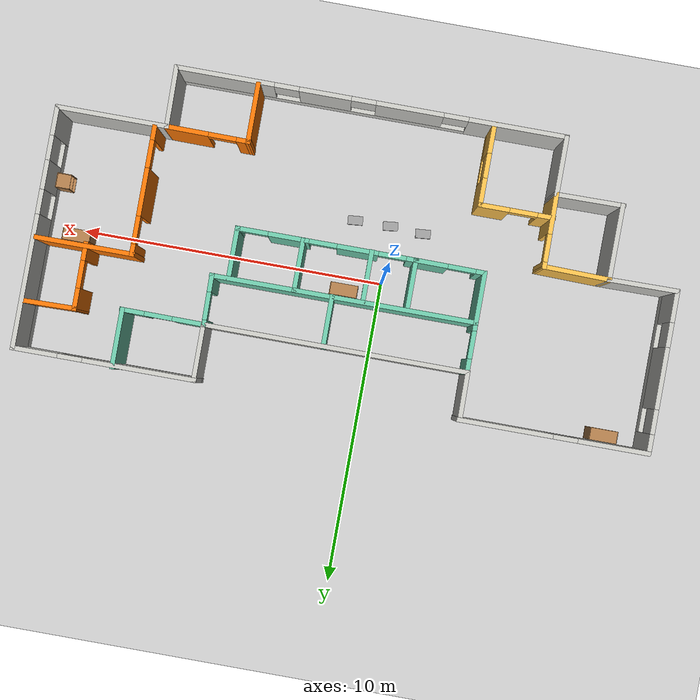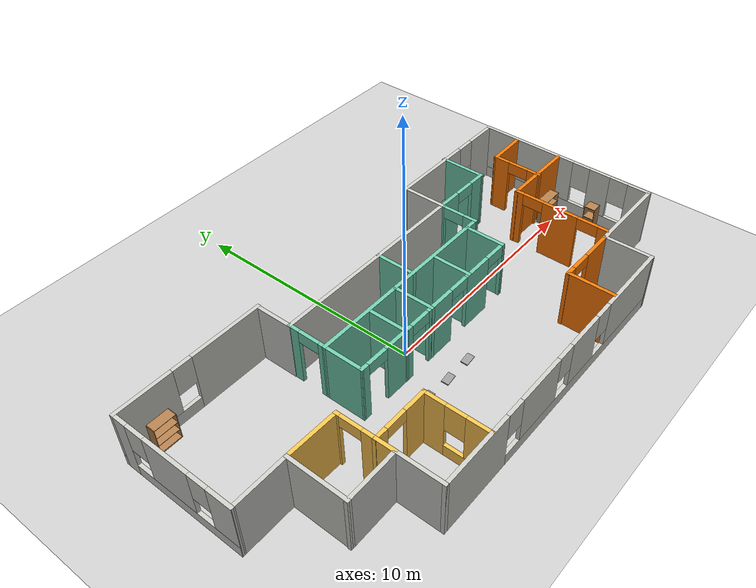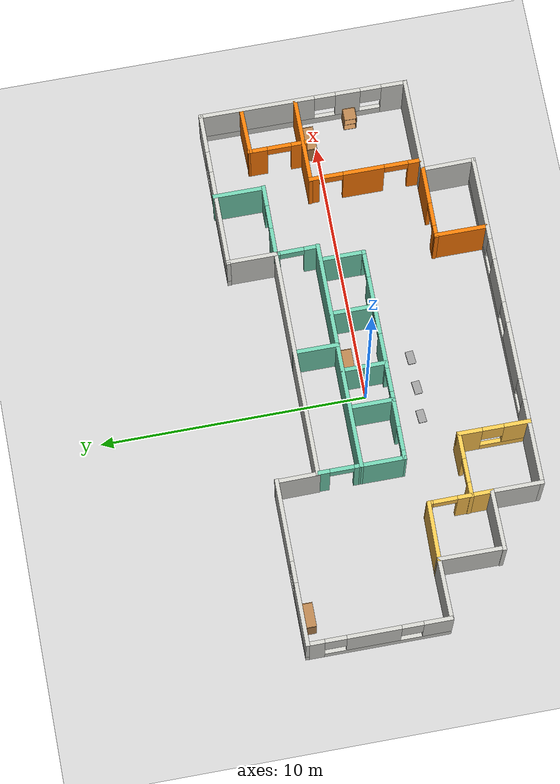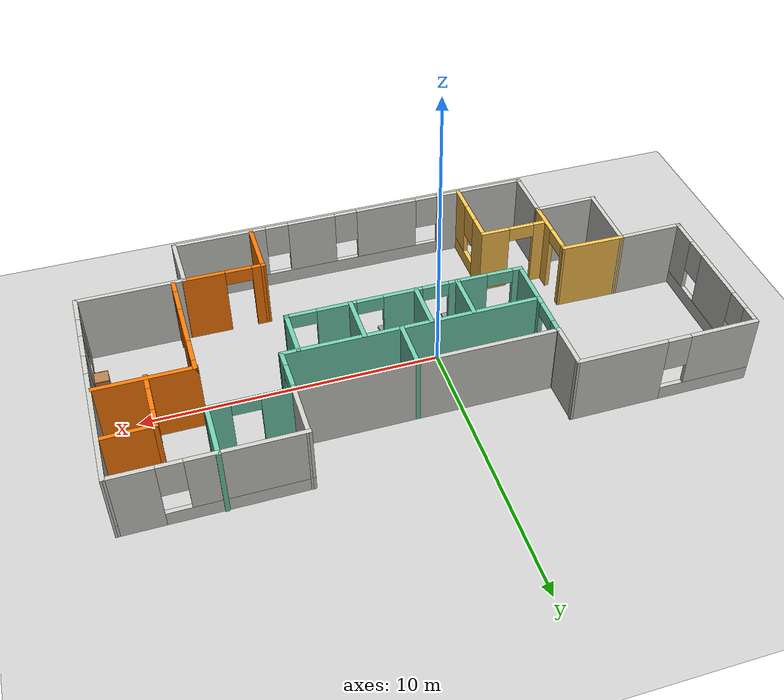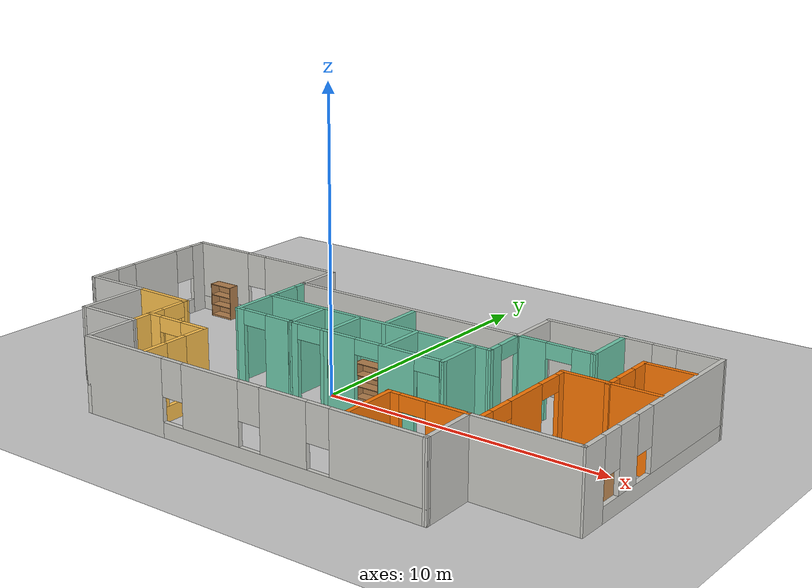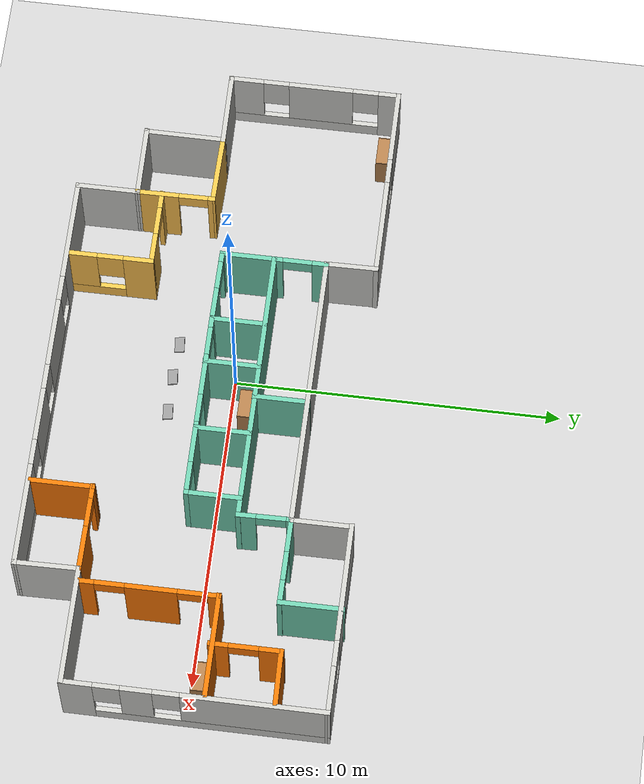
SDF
<sdf version="1.7">
 <world name="default">
  <plugin name="hello" filename="libhello.so"/>
  <light name="sun" type="directional">
   <pose>0 0 10 0 -0 0</pose>
   <diffuse>0.8 0.8 0.8 1</diffuse>
   <specular>0.2 0.2 0.2 1</specular>
   <attenuation>
    <range>1000</range>
    <constant>0.9</constant>
    <linear>0.01</linear>
    <quadratic>0.001</quadratic>
   </attenuation>
   <direction>-0.5 0.1 -0.9</direction>
   <spot><inner_angle>0</inner_angle><outer_angle>0</outer_angle><falloff>0</falloff></spot>
  </light>
  <model name="ground_plane">
   <static>1</static>
   <link name="link">
    <collision name="collision">
     <geometry><plane><normal>0 0 1</normal><size>100 100</size></plane></geometry>
     <surface>
      <contact><collide_bitmask>65535</collide_bitmask></contact>
      <friction><ode><mu>100</mu><mu2>50</mu2></ode></friction>
     </surface>
    </collision>
    <visual name="visual">
     <cast_shadows>0</cast_shadows>
     <geometry><plane><normal>0 0 1</normal><size>100 100</size></plane></geometry>
     <material>
      <script><uri>file://media/materials/scripts/gazebo.material</uri><name>Gazebo/Grey</name></script>
     </material>
    </visual>
   </link>
  </model>
  <sim_time>0</sim_time>
  <gravity>0 0 -9.8</gravity>
  <magnetic_field>6e-06 2.3e-05 -4.2e-05</magnetic_field>
  <atmosphere type="adiabatic"/>
  <physics type="ode">
   <max_step_size>0.001</max_step_size>
   <real_time_factor>1</real_time_factor>
   <real_time_update_rate>1000</real_time_update_rate>
  </physics>
  <scene><ambient>0.4 0.4 0.4 1</ambient><background>0.7 0.7 0.7 1</background><shadows>1</shadows></scene>
  <spherical_coordinates>
   <surface_model>EARTH_WGS84</surface_model>
   <latitude_deg>0</latitude_deg>
   <longitude_deg>0</longitude_deg>
   <elevation>0</elevation>
   <heading_deg>0</heading_deg>
  </spherical_coordinates>
  <model name="sweetHome">
   <pose>0.95206 -0.62895 0 0 -0 0</pose>
   <link name="Wall_1">
    <pose>-10.2246 1.88408 0 0 -0 -1.5708</pose>
    <visual name="Wall_1_Visual_0">
     <pose>-2.34402 0 1.25 0 -0 0</pose>
     <geometry><box><size>0.561956 0.15 2.5</size></box></geometry>
     <material>
      <script><uri>file://media/materials/scripts/gazebo.material</uri><name>Gazebo/CeilingTiled</name></script>
      <ambient>0.760784 0.662745 0.627451 1</ambient>
     </material>
     <meta><layer>0</layer></meta>
    </visual>
    <collision name="Wall_1_Collision_0">
     <geometry><box><size>0.561956 0.15 2.5</size></box></geometry>
     <pose>-2.34402 0 1.25 0 -0 0</pose>
    </collision>
    <visual name="Wall_1_Visual_1">
     <pose>0.280978 0 0.25 0 -0 0</pose>
     <geometry><box><size>4.68804 0.15 0.5</size></box></geometry>
     <material>
      <script><uri>file://media/materials/scripts/gazebo.material</uri><name>Gazebo/CeilingTiled</name></script>
      <ambient>0.760784 0.662745 0.627451 1</ambient>
     </material>
     <meta><layer>0</layer></meta>
    </visual>
    <collision name="Wall_1_Collision_1">
     <geometry><box><size>4.68804 0.15 0.5</size></box></geometry>
     <pose>0.280978 0 0.25 0 -0 0</pose>
    </collision>
    <visual name="Wall_1_Visual_2">
     <pose>-0.261194 0 1.5 0 -0 0</pose>
     <geometry><box><size>2.0037 0.15 2</size></box></geometry>
     <material>
      <script><uri>file://media/materials/scripts/gazebo.material</uri><name>Gazebo/CeilingTiled</name></script>
      <ambient>0.760784 0.662745 0.627451 1</ambient>
     </material>
     <meta><layer>0</layer></meta>
    </visual>
    <collision name="Wall_1_Collision_2">
     <geometry><box><size>2.0037 0.15 2</size></box></geometry>
     <pose>-0.261194 0 1.5 0 -0 0</pose>
    </collision>
    <visual name="Wall_1_Visual_3">
     <pose>2.08283 0 1.5 0 -0 0</pose>
     <geometry><box><size>1.08434 0.15 2</size></box></geometry>
     <material>
      <script><uri>file://media/materials/scripts/gazebo.material</uri><name>Gazebo/CeilingTiled</name></script>
      <ambient>0.760784 0.662745 0.627451 1</ambient>
     </material>
     <meta><layer>0</layer></meta>
    </visual>
    <collision name="Wall_1_Collision_3">
     <geometry><box><size>1.08434 0.15 2</size></box></geometry>
     <pose>2.08283 0 1.5 0 -0 0</pose>
    </collision>
    <visual name="Wall_1_Visual_4">
     <pose>-1.66304 0 1.9 0 -0 0</pose>
     <geometry><box><size>0.8 0.15 1.2</size></box></geometry>
     <material>
      <script><uri>file://media/materials/scripts/gazebo.material</uri><name>Gazebo/CeilingTiled</name></script>
      <ambient>0.760784 0.662745 0.627451 1</ambient>
     </material>
     <meta><layer>0</layer></meta>
    </visual>
    <collision name="Wall_1_Collision_4">
     <geometry><box><size>0.8 0.15 1.2</size></box></geometry>
     <pose>-1.66304 0 1.9 0 -0 0</pose>
    </collision>
    <visual name="Wall_1_Visual_5">
     <pose>1.14066 0 1.9 0 -0 0</pose>
     <geometry><box><size>0.8 0.15 1.2</size></box></geometry>
     <material>
      <script><uri>file://media/materials/scripts/gazebo.material</uri><name>Gazebo/CeilingTiled</name></script>
      <ambient>0.760784 0.662745 0.627451 1</ambient>
     </material>
     <meta><layer>0</layer></meta>
    </visual>
    <collision name="Wall_1_Collision_5">
     <geometry><box><size>0.8 0.15 1.2</size></box></geometry>
     <pose>1.14066 0 1.9 0 -0 0</pose>
    </collision>
   </link>
   <link name="Wall_10">
    <pose>7.29925 4.82446 0 0 -0 3.14159</pose>
    <visual name="Wall_10_Visual_0">
     <pose>-2.24505 0 1.25 0 -0 0</pose>
     <geometry><box><size>1.5099 0.15 2.5</size></box></geometry>
     <material>
      <script><uri>file://media/materials/scripts/gazebo.material</uri><name>Gazebo/CeilingTiled</name></script>
      <ambient>0.760784 0.662745 0.627451 1</ambient>
     </material>
     <meta><layer>0</layer></meta>
    </visual>
    <collision name="Wall_10_Collision_0">
     <geometry><box><size>1.5099 0.15 2.5</size></box></geometry>
     <pose>-2.24505 0 1.25 0 -0 0</pose>
    </collision>
    <visual name="Wall_10_Visual_1">
     <pose>0.754949 0 0.25 0 -0 0</pose>
     <geometry><box><size>4.4901 0.15 0.5</size></box></geometry>
     <material>
      <script><uri>file://media/materials/scripts/gazebo.material</uri><name>Gazebo/CeilingTiled</name></script>
      <ambient>0.760784 0.662745 0.627451 1</ambient>
     </material>
     <meta><layer>0</layer></meta>
    </visual>
    <collision name="Wall_10_Collision_1">
     <geometry><box><size>4.4901 0.15 0.5</size></box></geometry>
     <pose>0.754949 0 0.25 0 -0 0</pose>
    </collision>
    <visual name="Wall_10_Visual_2">
     <pose>1.15495 0 1.5 0 -0 0</pose>
     <geometry><box><size>3.6901 0.15 2</size></box></geometry>
     <material>
      <script><uri>file://media/materials/scripts/gazebo.material</uri><name>Gazebo/CeilingTiled</name></script>
      <ambient>0.760784 0.662745 0.627451 1</ambient>
     </material>
     <meta><layer>0</layer></meta>
    </visual>
    <collision name="Wall_10_Collision_2">
     <geometry><box><size>3.6901 0.15 2</size></box></geometry>
     <pose>1.15495 0 1.5 0 -0 0</pose>
    </collision>
    <visual name="Wall_10_Visual_3">
     <pose>-1.0901 0 1.9 0 -0 0</pose>
     <geometry><box><size>0.8 0.15 1.2</size></box></geometry>
     <material>
      <script><uri>file://media/materials/scripts/gazebo.material</uri><name>Gazebo/CeilingTiled</name></script>
      <ambient>0.760784 0.662745 0.627451 1</ambient>
     </material>
     <meta><layer>0</layer></meta>
    </visual>
    <collision name="Wall_10_Collision_3">
     <geometry><box><size>0.8 0.15 1.2</size></box></geometry>
     <pose>-1.0901 0 1.9 0 -0 0</pose>
    </collision>
   </link>
   <link name="Wall_11">
    <collision name="Wall_11_Collision">
     <geometry><box><size>1.94004 0.15 2.5</size></box></geometry>
     <pose>0 0 1.25 0 -0 0</pose>
    </collision>
    <visual name="Wall_11_Visual">
     <pose>0 0 1.25 0 -0 0</pose>
     <geometry><box><size>1.94004 0.15 2.5</size></box></geometry>
     <material>
      <script><uri>file://media/materials/scripts/gazebo.material</uri><name>Gazebo/CeilingTiled</name></script>
      <ambient>0.760784 0.662745 0.627451 1</ambient>
     </material>
     <meta><layer>0</layer></meta>
    </visual>
    <pose>4.393 3.92944 0 0 -0 -1.56939</pose>
   </link>
   <link name="Wall_12">
    <collision name="Wall_12_Collision">
     <geometry><box><size>8.64938 0.15 2.5</size></box></geometry>
     <pose>0 0 1.25 0 -0 0</pose>
    </collision>
    <visual name="Wall_12_Visual">
     <pose>0 0 1.25 0 -0 0</pose>
     <geometry><box><size>8.64938 0.15 2.5</size></box></geometry>
     <material>
      <script><uri>file://media/materials/scripts/gazebo.material</uri><name>Gazebo/CeilingTiled</name></script>
      <ambient>0.760784 0.662745 0.627451 1</ambient>
     </material>
     <meta><layer>0</layer></meta>
    </visual>
    <pose>0.144572 3.04219 0 0 -0 3.13976</pose>
   </link>
   <link name="Wall_13">
    <collision name="Wall_13_Collision">
     <geometry><box><size>1.66987 0.15 2.5</size></box></geometry>
     <pose>0 0 1.25 0 -0 0</pose>
    </collision>
    <visual name="Wall_13_Visual">
     <pose>0 0 1.25 0 -0 0</pose>
     <geometry><box><size>1.66987 0.15 2.5</size></box></geometry>
     <material>
      <script><uri>file://media/materials/scripts/gazebo.material</uri><name>Gazebo/CeilingTiled</name></script>
      <ambient>0.760784 0.662745 0.627451 1</ambient>
     </material>
     <meta><layer>0</layer></meta>
    </visual>
    <pose>-4.13315 3.80986 0 0 -0 1.58123</pose>
   </link>
   <link name="Wall_14">
    <pose>-7.17097 4.56975 0 0 -0 3.14159</pose>
    <visual name="Wall_14_Visual_0">
     <pose>-1.5746 0 1.25 0 -0 0</pose>
     <geometry><box><size>3.1008 0.15 2.5</size></box></geometry>
     <material>
      <script><uri>file://media/materials/scripts/gazebo.material</uri><name>Gazebo/CeilingTiled</name></script>
      <ambient>0.760784 0.662745 0.627451 1</ambient>
     </material>
     <meta><layer>0</layer></meta>
    </visual>
    <collision name="Wall_14_Collision_0">
     <geometry><box><size>3.1008 0.15 2.5</size></box></geometry>
     <pose>-1.5746 0 1.25 0 -0 0</pose>
    </collision>
    <visual name="Wall_14_Visual_1">
     <pose>1.5504 0 0.25 0 -0 0</pose>
     <geometry><box><size>3.1492 0.15 0.5</size></box></geometry>
     <material>
      <script><uri>file://media/materials/scripts/gazebo.material</uri><name>Gazebo/CeilingTiled</name></script>
      <ambient>0.760784 0.662745 0.627451 1</ambient>
     </material>
     <meta><layer>0</layer></meta>
    </visual>
    <collision name="Wall_14_Collision_1">
     <geometry><box><size>3.1492 0.15 0.5</size></box></geometry>
     <pose>1.5504 0 0.25 0 -0 0</pose>
    </collision>
    <visual name="Wall_14_Visual_2">
     <pose>1.9504 0 1.5 0 -0 0</pose>
     <geometry><box><size>2.3492 0.15 2</size></box></geometry>
     <material>
      <script><uri>file://media/materials/scripts/gazebo.material</uri><name>Gazebo/CeilingTiled</name></script>
      <ambient>0.760784 0.662745 0.627451 1</ambient>
     </material>
     <meta><layer>0</layer></meta>
    </visual>
    <collision name="Wall_14_Collision_2">
     <geometry><box><size>2.3492 0.15 2</size></box></geometry>
     <pose>1.9504 0 1.5 0 -0 0</pose>
    </collision>
    <visual name="Wall_14_Visual_3">
     <pose>0.375799 0 1.9 0 -0 0</pose>
     <geometry><box><size>0.8 0.15 1.2</size></box></geometry>
     <material>
      <script><uri>file://media/materials/scripts/gazebo.material</uri><name>Gazebo/CeilingTiled</name></script>
      <ambient>0.760784 0.662745 0.627451 1</ambient>
     </material>
     <meta><layer>0</layer></meta>
    </visual>
    <collision name="Wall_14_Collision_3">
     <geometry><box><size>0.8 0.15 1.2</size></box></geometry>
     <pose>0.375799 0 1.9 0 -0 0</pose>
    </collision>
   </link>
   <link name="Wall_2">
    <collision name="Wall_2_Collision">
     <geometry><box><size>2.32468 0.15 2.5</size></box></geometry>
     <pose>0 0 1.25 0 -0 0</pose>
    </collision>
    <visual name="Wall_2_Visual">
     <pose>0 0 1.25 0 -0 0</pose>
     <geometry><box><size>2.32468 0.15 2.5</size></box></geometry>
     <material>
      <script><uri>file://media/materials/scripts/gazebo.material</uri><name>Gazebo/CeilingTiled</name></script>
      <ambient>0.760784 0.662745 0.627451 1</ambient>
     </material>
     <meta><layer>0</layer></meta>
    </visual>
    <pose>-9.11715 -0.655861 0 0 -0 0.009249</pose>
   </link>
   <link name="Wall_21">
    <collision name="Wall_21_Collision">
     <geometry><box><size>2.25039 0.15 2.5</size></box></geometry>
     <pose>0 0 1.25 0 -0 0</pose>
    </collision>
    <visual name="Wall_21_Visual">
     <pose>0 0 1.25 0 -0 0</pose>
     <geometry><box><size>2.25039 0.15 2.5</size></box></geometry>
     <material>
      <script><uri>file://media/materials/scripts/gazebo.material</uri><name>Gazebo/Grey</name></script>
      <ambient>1 0.764706 0.305882 1</ambient>
     </material>
     <meta><layer>0</layer></meta>
    </visual>
    <pose>-6.9798 -0.665918 0 0 -0 -0.019153</pose>
   </link>
   <link name="Wall_23">
    <pose>-5.91975 -1.85097 0 0 -0 -1.56216</pose>
    <visual name="Wall_23_Visual_0">
     <pose>-1.12656 0 1.25 0 -0 0</pose>
     <geometry><box><size>0.226848 0.15 2.5</size></box></geometry>
     <material>
      <script><uri>file://media/materials/scripts/gazebo.material</uri><name>Gazebo/Grey</name></script>
      <ambient>1 0.764706 0.305882 1</ambient>
     </material>
     <meta><layer>0</layer></meta>
    </visual>
    <collision name="Wall_23_Collision_0">
     <geometry><box><size>0.226848 0.15 2.5</size></box></geometry>
     <pose>-1.12656 0 1.25 0 -0 0</pose>
    </collision>
    <visual name="Wall_23_Visual_1">
     <pose>0.563424 0 1.25 0 -0 0</pose>
     <geometry><box><size>1.35312 0.15 2.5</size></box></geometry>
     <material>
      <script><uri>file://media/materials/scripts/gazebo.material</uri><name>Gazebo/Grey</name></script>
      <ambient>1 0.764706 0.305882 1</ambient>
     </material>
     <meta><layer>0</layer></meta>
    </visual>
    <collision name="Wall_23_Collision_1">
     <geometry><box><size>1.35312 0.15 2.5</size></box></geometry>
     <pose>0.563424 0 1.25 0 -0 0</pose>
    </collision>
    <visual name="Wall_23_Visual_2">
     <pose>-0.563139 0 2.25 0 -0 0</pose>
     <geometry><box><size>0.9 0.15 0.5</size></box></geometry>
     <material>
      <script><uri>file://media/materials/scripts/gazebo.material</uri><name>Gazebo/Grey</name></script>
      <ambient>1 0.764706 0.305882 1</ambient>
     </material>
     <meta><layer>0</layer></meta>
    </visual>
    <collision name="Wall_23_Collision_2">
     <geometry><box><size>0.9 0.15 0.5</size></box></geometry>
     <pose>-0.563139 0 2.25 0 -0 0</pose>
    </collision>
   </link>
   <link name="Wall_25">
    <pose>-4.75775 -2.26176 0 0 -0 0</pose>
    <visual name="Wall_25_Visual_0">
     <pose>-0.962736 0 1.25 0 -0 0</pose>
     <geometry><box><size>0.574527 0.15 2.5</size></box></geometry>
     <material>
      <script><uri>file://media/materials/scripts/gazebo.material</uri><name>Gazebo/Grey</name></script>
      <ambient>1 0.764706 0.305882 1</ambient>
     </material>
     <meta><layer>0</layer></meta>
    </visual>
    <collision name="Wall_25_Collision_0">
     <geometry><box><size>0.574527 0.15 2.5</size></box></geometry>
     <pose>-0.962736 0 1.25 0 -0 0</pose>
    </collision>
    <visual name="Wall_25_Visual_1">
     <pose>0.737264 0 1.25 0 -0 0</pose>
     <geometry><box><size>1.02547 0.15 2.5</size></box></geometry>
     <material>
      <script><uri>file://media/materials/scripts/gazebo.material</uri><name>Gazebo/Grey</name></script>
      <ambient>1 0.764706 0.305882 1</ambient>
     </material>
     <meta><layer>0</layer></meta>
    </visual>
    <collision name="Wall_25_Collision_1">
     <geometry><box><size>1.02547 0.15 2.5</size></box></geometry>
     <pose>0.737264 0 1.25 0 -0 0</pose>
    </collision>
    <visual name="Wall_25_Visual_2">
     <pose>-0.225473 0 2.25 0 -0 0</pose>
     <geometry><box><size>0.9 0.15 0.5</size></box></geometry>
     <material>
      <script><uri>file://media/materials/scripts/gazebo.material</uri><name>Gazebo/Grey</name></script>
      <ambient>1 0.764706 0.305882 1</ambient>
     </material>
     <meta><layer>0</layer></meta>
    </visual>
    <collision name="Wall_25_Collision_2">
     <geometry><box><size>0.9 0.15 0.5</size></box></geometry>
     <pose>-0.225473 0 2.25 0 -0 0</pose>
    </collision>
   </link>
   <link name="Wall_26">
    <pose>-3.58275 -3.56176 0 0 -0 -1.5708</pose>
    <visual name="Wall_26_Visual_0">
     <pose>-0.904253 0 1.25 0 -0 0</pose>
     <geometry><box><size>0.941493 0.15 2.5</size></box></geometry>
     <material>
      <script><uri>file://media/materials/scripts/gazebo.material</uri><name>Gazebo/Grey</name></script>
      <ambient>1 0.764706 0.305882 1</ambient>
     </material>
     <meta><layer>0</layer></meta>
    </visual>
    <collision name="Wall_26_Collision_0">
     <geometry><box><size>0.941493 0.15 2.5</size></box></geometry>
     <pose>-0.904253 0 1.25 0 -0 0</pose>
    </collision>
    <visual name="Wall_26_Visual_1">
     <pose>0.470747 0 0.25 0 -0 0</pose>
     <geometry><box><size>1.80851 0.15 0.5</size></box></geometry>
     <material>
      <script><uri>file://media/materials/scripts/gazebo.material</uri><name>Gazebo/Grey</name></script>
      <ambient>1 0.764706 0.305882 1</ambient>
     </material>
     <meta><layer>0</layer></meta>
    </visual>
    <collision name="Wall_26_Collision_1">
     <geometry><box><size>1.80851 0.15 0.5</size></box></geometry>
     <pose>0.470747 0 0.25 0 -0 0</pose>
    </collision>
    <visual name="Wall_26_Visual_2">
     <pose>0.870747 0 1.5 0 -0 0</pose>
     <geometry><box><size>1.00851 0.15 2</size></box></geometry>
     <material>
      <script><uri>file://media/materials/scripts/gazebo.material</uri><name>Gazebo/Grey</name></script>
      <ambient>1 0.764706 0.305882 1</ambient>
     </material>
     <meta><layer>0</layer></meta>
    </visual>
    <collision name="Wall_26_Collision_2">
     <geometry><box><size>1.00851 0.15 2</size></box></geometry>
     <pose>0.870747 0 1.5 0 -0 0</pose>
    </collision>
    <visual name="Wall_26_Visual_3">
     <pose>-0.033507 0 1.9 0 -0 0</pose>
     <geometry><box><size>0.8 0.15 1.2</size></box></geometry>
     <material>
      <script><uri>file://media/materials/scripts/gazebo.material</uri><name>Gazebo/Grey</name></script>
      <ambient>1 0.764706 0.305882 1</ambient>
     </material>
     <meta><layer>0</layer></meta>
    </visual>
    <collision name="Wall_26_Collision_3">
     <geometry><box><size>0.8 0.15 1.2</size></box></geometry>
     <pose>-0.033507 0 1.9 0 -0 0</pose>
    </collision>
   </link>
   <link name="Wall_28">
    <pose>-4.10511 2.24996 0 0 -0 -1.5708</pose>
    <visual name="Wall_28_Visual_0">
     <pose>-0.618972 0 1.25 0 -0 0</pose>
     <geometry><box><size>0.512055 0.15 2.5</size></box></geometry>
     <material>
      <script><uri>file://media/materials/scripts/gazebo.material</uri><name>Gazebo/Grey</name></script>
      <ambient>0.435294 0.796078 0.67451 1</ambient>
     </material>
     <meta><layer>0</layer></meta>
    </visual>
    <collision name="Wall_28_Collision_0">
     <geometry><box><size>0.512055 0.15 2.5</size></box></geometry>
     <pose>-0.618972 0 1.25 0 -0 0</pose>
    </collision>
    <visual name="Wall_28_Visual_1">
     <pose>0.706028 0 1.25 0 -0 0</pose>
     <geometry><box><size>0.337945 0.15 2.5</size></box></geometry>
     <material>
      <script><uri>file://media/materials/scripts/gazebo.material</uri><name>Gazebo/Grey</name></script>
      <ambient>0.435294 0.796078 0.67451 1</ambient>
     </material>
     <meta><layer>0</layer></meta>
    </visual>
    <collision name="Wall_28_Collision_1">
     <geometry><box><size>0.337945 0.15 2.5</size></box></geometry>
     <pose>0.706028 0 1.25 0 -0 0</pose>
    </collision>
    <visual name="Wall_28_Visual_2">
     <pose>0.087055 0 2.25 0 -0 0</pose>
     <geometry><box><size>0.9 0.15 0.5</size></box></geometry>
     <material>
      <script><uri>file://media/materials/scripts/gazebo.material</uri><name>Gazebo/Grey</name></script>
      <ambient>0.435294 0.796078 0.67451 1</ambient>
     </material>
     <meta><layer>0</layer></meta>
    </visual>
    <collision name="Wall_28_Collision_2">
     <geometry><box><size>0.9 0.15 0.5</size></box></geometry>
     <pose>0.087055 0 2.25 0 -0 0</pose>
    </collision>
   </link>
   <link name="Wall_29">
    <collision name="Wall_29_Collision">
     <geometry><box><size>8.67077 0.15 2.5</size></box></geometry>
     <pose>0 0 1.25 0 -0 0</pose>
    </collision>
    <visual name="Wall_29_Visual">
     <pose>0 0 1.25 0 -0 0</pose>
     <geometry><box><size>8.67077 0.15 2.5</size></box></geometry>
     <material>
      <script><uri>file://media/materials/scripts/gazebo.material</uri><name>Gazebo/Grey</name></script>
      <ambient>0.435294 0.796078 0.67451 1</ambient>
     </material>
     <meta><layer>0</layer></meta>
    </visual>
    <pose>0.155275 1.45141 0 0 -0 0.000339</pose>
   </link>
   <link name="Wall_3">
    <collision name="Wall_3_Collision">
     <geometry><box><size>2.52014 0.15 2.5</size></box></geometry>
     <pose>0 0 1.25 0 -0 0</pose>
    </collision>
    <visual name="Wall_3_Visual">
     <pose>0 0 1.25 0 -0 0</pose>
     <geometry><box><size>2.52014 0.15 2.5</size></box></geometry>
     <material>
      <script><uri>file://media/materials/scripts/gazebo.material</uri><name>Gazebo/CeilingTiled</name></script>
      <ambient>0.760784 0.662745 0.627451 1</ambient>
     </material>
     <meta><layer>0</layer></meta>
    </visual>
    <pose>-8.03554 -1.85097 0 0 -0 -1.57564</pose>
   </link>
   <link name="Wall_30">
    <pose>4.39496 2.24364 0 0 -0 1.58433</pose>
    <visual name="Wall_30_Visual_0">
     <pose>-0.563086 0 1.25 0 -0 0</pose>
     <geometry><box><size>0.605546 0.15 2.5</size></box></geometry>
     <material>
      <script><uri>file://media/materials/scripts/gazebo.material</uri><name>Gazebo/Grey</name></script>
      <ambient>0.435294 0.796078 0.67451 1</ambient>
     </material>
     <meta><layer>0</layer></meta>
    </visual>
    <collision name="Wall_30_Collision_0">
     <geometry><box><size>0.605546 0.15 2.5</size></box></geometry>
     <pose>-0.563086 0 1.25 0 -0 0</pose>
    </collision>
    <visual name="Wall_30_Visual_1">
     <pose>0.752773 0 1.25 0 -0 0</pose>
     <geometry><box><size>0.226171 0.15 2.5</size></box></geometry>
     <material>
      <script><uri>file://media/materials/scripts/gazebo.material</uri><name>Gazebo/Grey</name></script>
      <ambient>0.435294 0.796078 0.67451 1</ambient>
     </material>
     <meta><layer>0</layer></meta>
    </visual>
    <collision name="Wall_30_Collision_1">
     <geometry><box><size>0.226171 0.15 2.5</size></box></geometry>
     <pose>0.752773 0 1.25 0 -0 0</pose>
    </collision>
    <visual name="Wall_30_Visual_2">
     <pose>0.189687 0 2.25 0 -0 0</pose>
     <geometry><box><size>0.9 0.15 0.5</size></box></geometry>
     <material>
      <script><uri>file://media/materials/scripts/gazebo.material</uri><name>Gazebo/Grey</name></script>
      <ambient>0.435294 0.796078 0.67451 1</ambient>
     </material>
     <meta><layer>0</layer></meta>
    </visual>
    <collision name="Wall_30_Collision_2">
     <geometry><box><size>0.9 0.15 0.5</size></box></geometry>
     <pose>0.189687 0 2.25 0 -0 0</pose>
    </collision>
   </link>
   <link name="Wall_32">
    <collision name="Wall_32_Collision">
     <geometry><box><size>1.75 0.15 2.5</size></box></geometry>
     <pose>0 0 1.25 0 -0 0</pose>
    </collision>
    <visual name="Wall_32_Visual">
     <pose>0 0 1.25 0 -0 0</pose>
     <geometry><box><size>1.75 0.15 2.5</size></box></geometry>
     <material>
      <script><uri>file://media/materials/scripts/gazebo.material</uri><name>Gazebo/Grey</name></script>
      <ambient>0.435294 0.796078 0.67451 1</ambient>
     </material>
     <meta><layer>0</layer></meta>
    </visual>
    <pose>0.53458 2.2428 0 0 -0 -1.5708</pose>
   </link>
   <link name="Wall_36">
    <pose>5.70639 3.02568 0 0 -0 -0.006614</pose>
    <visual name="Wall_36_Visual_0">
     <pose>-0.849808 0 1.25 0 -0 0</pose>
     <geometry><box><size>1.09471 0.15 2.5</size></box></geometry>
     <material>
      <script><uri>file://media/materials/scripts/gazebo.material</uri><name>Gazebo/Grey</name></script>
      <ambient>0.435294 0.796078 0.67451 1</ambient>
     </material>
     <meta><layer>0</layer></meta>
    </visual>
    <collision name="Wall_36_Collision_0">
     <geometry><box><size>1.09471 0.15 2.5</size></box></geometry>
     <pose>-0.849808 0 1.25 0 -0 0</pose>
    </collision>
    <visual name="Wall_36_Visual_1">
     <pose>0.997353 0 1.25 0 -0 0</pose>
     <geometry><box><size>0.799616 0.15 2.5</size></box></geometry>
     <material>
      <script><uri>file://media/materials/scripts/gazebo.material</uri><name>Gazebo/Grey</name></script>
      <ambient>0.435294 0.796078 0.67451 1</ambient>
     </material>
     <meta><layer>0</layer></meta>
    </visual>
    <collision name="Wall_36_Collision_1">
     <geometry><box><size>0.799616 0.15 2.5</size></box></geometry>
     <pose>0.997353 0 1.25 0 -0 0</pose>
    </collision>
    <visual name="Wall_36_Visual_2">
     <pose>0.147546 0 2.25 0 -0 0</pose>
     <geometry><box><size>0.9 0.15 0.5</size></box></geometry>
     <material>
      <script><uri>file://media/materials/scripts/gazebo.material</uri><name>Gazebo/Grey</name></script>
      <ambient>0.435294 0.796078 0.67451 1</ambient>
     </material>
     <meta><layer>0</layer></meta>
    </visual>
    <collision name="Wall_36_Collision_2">
     <geometry><box><size>0.9 0.15 0.5</size></box></geometry>
     <pose>0.147546 0 2.25 0 -0 0</pose>
    </collision>
   </link>
   <link name="Wall_37">
    <collision name="Wall_37_Collision">
     <geometry><box><size>2 0.15 2.5</size></box></geometry>
     <pose>0 0 1.25 0 -0 0</pose>
    </collision>
    <visual name="Wall_37_Visual">
     <pose>0 0 1.25 0 -0 0</pose>
     <geometry><box><size>2 0.15 2.5</size></box></geometry>
     <material>
      <script><uri>file://media/materials/scripts/gazebo.material</uri><name>Gazebo/Grey</name></script>
      <ambient>0.435294 0.796078 0.67451 1</ambient>
     </material>
     <meta><layer>0</layer></meta>
    </visual>
    <pose>7.01103 3.94193 0 0 -0 1.5708</pose>
   </link>
   <link name="Wall_4">
    <collision name="Wall_4_Collision">
     <geometry><box><size>2.3018 0.15 2.5</size></box></geometry>
     <pose>0 0 1.25 0 -0 0</pose>
    </collision>
    <visual name="Wall_4_Visual">
     <pose>0 0 1.25 0 -0 0</pose>
     <geometry><box><size>2.3018 0.15 2.5</size></box></geometry>
     <material>
      <script><uri>file://media/materials/scripts/gazebo.material</uri><name>Gazebo/CeilingTiled</name></script>
      <ambient>0.760784 0.662745 0.627451 1</ambient>
     </material>
     <meta><layer>0</layer></meta>
    </visual>
    <pose>-6.98554 -3.02597 0 0 -0 0.009347</pose>
   </link>
   <link name="Wall_40">
    <collision name="Wall_40_Collision">
     <geometry><box><size>2 0.15 2.5</size></box></geometry>
     <pose>0 0 1.25 0 -0 0</pose>
    </collision>
    <visual name="Wall_40_Visual">
     <pose>0 0 1.25 0 -0 0</pose>
     <geometry><box><size>2 0.15 2.5</size></box></geometry>
     <material>
      <script><uri>file://media/materials/scripts/gazebo.material</uri><name>Gazebo/Grey</name></script>
      <ambient>0.996078 0.47451 0.0196078 1</ambient>
     </material>
     <meta><layer>0</layer></meta>
    </visual>
    <pose>4.03391 -3.85788 0 0 -0 1.5708</pose>
   </link>
   <link name="Wall_41">
    <pose>5.33391 -2.94294 0 0 -0 -0.007618</pose>
    <visual name="Wall_41_Visual_0">
     <pose>-1.15923 0 1.25 0 -0 0</pose>
     <geometry><box><size>0.471849 0.15 2.5</size></box></geometry>
     <material>
      <script><uri>file://media/materials/scripts/gazebo.material</uri><name>Gazebo/Grey</name></script>
      <ambient>0.996078 0.47451 0.0196078 1</ambient>
     </material>
     <meta><layer>0</layer></meta>
    </visual>
    <collision name="Wall_41_Collision_0">
     <geometry><box><size>0.471849 0.15 2.5</size></box></geometry>
     <pose>-1.15923 0 1.25 0 -0 0</pose>
    </collision>
    <visual name="Wall_41_Visual_1">
     <pose>0.685925 0 1.25 0 -0 0</pose>
     <geometry><box><size>1.41846 0.15 2.5</size></box></geometry>
     <material>
      <script><uri>file://media/materials/scripts/gazebo.material</uri><name>Gazebo/Grey</name></script>
      <ambient>0.996078 0.47451 0.0196078 1</ambient>
     </material>
     <meta><layer>0</layer></meta>
    </visual>
    <collision name="Wall_41_Collision_1">
     <geometry><box><size>1.41846 0.15 2.5</size></box></geometry>
     <pose>0.685925 0 1.25 0 -0 0</pose>
    </collision>
    <visual name="Wall_41_Visual_2">
     <pose>-0.473303 0 2.25 0 -0 0</pose>
     <geometry><box><size>0.9 0.15 0.5</size></box></geometry>
     <material>
      <script><uri>file://media/materials/scripts/gazebo.material</uri><name>Gazebo/Grey</name></script>
      <ambient>0.996078 0.47451 0.0196078 1</ambient>
     </material>
     <meta><layer>0</layer></meta>
    </visual>
    <collision name="Wall_41_Collision_2">
     <geometry><box><size>0.9 0.15 0.5</size></box></geometry>
     <pose>-0.473303 0 2.25 0 -0 0</pose>
    </collision>
   </link>
   <link name="Wall_43">
    <pose>7.03294 -0.810944 0 0 -0 1.5708</pose>
    <visual name="Wall_43_Visual_0">
     <pose>-1.88266 0 1.25 0 -0 0</pose>
     <geometry><box><size>0.484677 0.15 2.5</size></box></geometry>
     <material>
      <script><uri>file://media/materials/scripts/gazebo.material</uri><name>Gazebo/Grey</name></script>
      <ambient>0.996078 0.47451 0.0196078 1</ambient>
     </material>
     <meta><layer>0</layer></meta>
    </visual>
    <collision name="Wall_43_Collision_0">
     <geometry><box><size>0.484677 0.15 2.5</size></box></geometry>
     <pose>-1.88266 0 1.25 0 -0 0</pose>
    </collision>
    <visual name="Wall_43_Visual_1">
     <pose>0.039677 0 1.25 0 -0 0</pose>
     <geometry><box><size>1.56 0.15 2.5</size></box></geometry>
     <material>
      <script><uri>file://media/materials/scripts/gazebo.material</uri><name>Gazebo/Grey</name></script>
      <ambient>0.996078 0.47451 0.0196078 1</ambient>
     </material>
     <meta><layer>0</layer></meta>
    </visual>
    <collision name="Wall_43_Collision_1">
     <geometry><box><size>1.56 0.15 2.5</size></box></geometry>
     <pose>0.039677 0 1.25 0 -0 0</pose>
    </collision>
    <visual name="Wall_43_Visual_2">
     <pose>1.92234 0 1.25 0 -0 0</pose>
     <geometry><box><size>0.405323 0.15 2.5</size></box></geometry>
     <material>
      <script><uri>file://media/materials/scripts/gazebo.material</uri><name>Gazebo/Grey</name></script>
      <ambient>0.996078 0.47451 0.0196078 1</ambient>
     </material>
     <meta><layer>0</layer></meta>
    </visual>
    <collision name="Wall_43_Collision_2">
     <geometry><box><size>0.405323 0.15 2.5</size></box></geometry>
     <pose>1.92234 0 1.25 0 -0 0</pose>
    </collision>
    <visual name="Wall_43_Visual_3">
     <pose>-1.19032 0 2.25 0 -0 0</pose>
     <geometry><box><size>0.9 0.15 0.5</size></box></geometry>
     <material>
      <script><uri>file://media/materials/scripts/gazebo.material</uri><name>Gazebo/Grey</name></script>
      <ambient>0.996078 0.47451 0.0196078 1</ambient>
     </material>
     <meta><layer>0</layer></meta>
    </visual>
    <collision name="Wall_43_Collision_3">
     <geometry><box><size>0.9 0.15 0.5</size></box></geometry>
     <pose>-1.19032 0 2.25 0 -0 0</pose>
    </collision>
    <visual name="Wall_43_Visual_4">
     <pose>1.26968 0 2.25 0 -0 0</pose>
     <geometry><box><size>0.9 0.15 0.5</size></box></geometry>
     <material>
      <script><uri>file://media/materials/scripts/gazebo.material</uri><name>Gazebo/Grey</name></script>
      <ambient>0.996078 0.47451 0.0196078 1</ambient>
     </material>
     <meta><layer>0</layer></meta>
    </visual>
    <collision name="Wall_43_Collision_4">
     <geometry><box><size>0.9 0.15 0.5</size></box></geometry>
     <pose>1.26968 0 2.25 0 -0 0</pose>
    </collision>
   </link>
   <link name="Wall_44">
    <collision name="Wall_44_Collision">
     <geometry><box><size>3.25 0.15 2.5</size></box></geometry>
     <pose>0 0 1.25 0 -0 0</pose>
    </collision>
    <visual name="Wall_44_Visual">
     <pose>0 0 1.25 0 -0 0</pose>
     <geometry><box><size>3.25 0.15 2.5</size></box></geometry>
     <material>
      <script><uri>file://media/materials/scripts/gazebo.material</uri><name>Gazebo/Grey</name></script>
      <ambient>0.996078 0.47451 0.0196078 1</ambient>
     </material>
     <meta><layer>0</layer></meta>
    </visual>
    <pose>8.5598 1.23906 0 0 -0 0</pose>
   </link>
   <link name="Wall_46">
    <pose>8.51859 2.22157 0 0 -0 1.5708</pose>
    <visual name="Wall_46_Visual_0">
     <pose>-0.822334 0 1.25 0 -0 0</pose>
     <geometry><box><size>0.605333 0.15 2.5</size></box></geometry>
     <material>
      <script><uri>file://media/materials/scripts/gazebo.material</uri><name>Gazebo/Grey</name></script>
      <ambient>0.996078 0.47451 0.0196078 1</ambient>
     </material>
     <meta><layer>0</layer></meta>
    </visual>
    <collision name="Wall_46_Collision_0">
     <geometry><box><size>0.605333 0.15 2.5</size></box></geometry>
     <pose>-0.822334 0 1.25 0 -0 0</pose>
    </collision>
    <visual name="Wall_46_Visual_1">
     <pose>0.752666 0 1.25 0 -0 0</pose>
     <geometry><box><size>0.744667 0.15 2.5</size></box></geometry>
     <material>
      <script><uri>file://media/materials/scripts/gazebo.material</uri><name>Gazebo/Grey</name></script>
      <ambient>0.996078 0.47451 0.0196078 1</ambient>
     </material>
     <meta><layer>0</layer></meta>
    </visual>
    <collision name="Wall_46_Collision_1">
     <geometry><box><size>0.744667 0.15 2.5</size></box></geometry>
     <pose>0.752666 0 1.25 0 -0 0</pose>
    </collision>
    <visual name="Wall_46_Visual_2">
     <pose>-0.069667 0 2.25 0 -0 0</pose>
     <geometry><box><size>0.9 0.15 0.5</size></box></geometry>
     <material>
      <script><uri>file://media/materials/scripts/gazebo.material</uri><name>Gazebo/Grey</name></script>
      <ambient>0.996078 0.47451 0.0196078 1</ambient>
     </material>
     <meta><layer>0</layer></meta>
    </visual>
    <collision name="Wall_46_Collision_2">
     <geometry><box><size>0.9 0.15 0.5</size></box></geometry>
     <pose>-0.069667 0 2.25 0 -0 0</pose>
    </collision>
   </link>
   <link name="Wall_47">
    <collision name="Wall_47_Collision">
     <geometry><box><size>1.75 0.15 2.5</size></box></geometry>
     <pose>0 0 1.25 0 -0 0</pose>
    </collision>
    <visual name="Wall_47_Visual">
     <pose>0 0 1.25 0 -0 0</pose>
     <geometry><box><size>1.75 0.15 2.5</size></box></geometry>
     <material>
      <script><uri>file://media/materials/scripts/gazebo.material</uri><name>Gazebo/Grey</name></script>
      <ambient>0.996078 0.47451 0.0196078 1</ambient>
     </material>
     <meta><layer>0</layer></meta>
    </visual>
    <pose>9.31859 3.27157 0 0 -0 0.021859</pose>
   </link>
   <link name="Wall_49">
    <collision name="Wall_49_Collision">
     <geometry><box><size>1.75 0.15 2.5</size></box></geometry>
     <pose>0 0 1.25 0 -0 0</pose>
    </collision>
    <visual name="Wall_49_Visual">
     <pose>0 0 1.25 0 -0 0</pose>
     <geometry><box><size>1.75 0.15 2.5</size></box></geometry>
     <material>
      <script><uri>file://media/materials/scripts/gazebo.material</uri><name>Gazebo/Grey</name></script>
      <ambient>0.435294 0.796078 0.67451 1</ambient>
     </material>
     <meta><layer>0</layer></meta>
    </visual>
    <pose>-1.88542 0.632795 0 0 -0 -1.5708</pose>
   </link>
   <link name="Wall_5">
    <collision name="Wall_5_Collision">
     <geometry><box><size>2 0.15 2.5</size></box></geometry>
     <pose>0 0 1.25 0 -0 0</pose>
    </collision>
    <visual name="Wall_5_Visual">
     <pose>0 0 1.25 0 -0 0</pose>
     <geometry><box><size>2 0.15 2.5</size></box></geometry>
     <material>
      <script><uri>file://media/materials/scripts/gazebo.material</uri><name>Gazebo/CeilingTiled</name></script>
      <ambient>1 0.764706 0.305882 1</ambient>
     </material>
     <meta><layer>0</layer></meta>
    </visual>
    <pose>-5.90969 -3.94092 0 0 -0 -1.5708</pose>
   </link>
   <link name="Wall_50">
    <pose>0.98958 -0.167205 0 0 -0 0</pose>
    <visual name="Wall_50_Visual_0">
     <pose>-2.7625 0 1.25 0 -0 0</pose>
     <geometry><box><size>0.395 0.15 2.5</size></box></geometry>
     <material>
      <script><uri>file://media/materials/scripts/gazebo.material</uri><name>Gazebo/Grey</name></script>
      <ambient>0.435294 0.796078 0.67451 1</ambient>
     </material>
     <meta><layer>0</layer></meta>
    </visual>
    <collision name="Wall_50_Collision_0">
     <geometry><box><size>0.395 0.15 2.5</size></box></geometry>
     <pose>-2.7625 0 1.25 0 -0 0</pose>
    </collision>
    <visual name="Wall_50_Visual_1">
     <pose>-0.995 0 1.25 0 -0 0</pose>
     <geometry><box><size>1.34 0.15 2.5</size></box></geometry>
     <material>
      <script><uri>file://media/materials/scripts/gazebo.material</uri><name>Gazebo/Grey</name></script>
      <ambient>0.435294 0.796078 0.67451 1</ambient>
     </material>
     <meta><layer>0</layer></meta>
    </visual>
    <collision name="Wall_50_Collision_1">
     <geometry><box><size>1.34 0.15 2.5</size></box></geometry>
     <pose>-0.995 0 1.25 0 -0 0</pose>
    </collision>
    <visual name="Wall_50_Visual_2">
     <pose>1.23694 0 1.25 0 -0 0</pose>
     <geometry><box><size>1.32389 0.15 2.5</size></box></geometry>
     <material>
      <script><uri>file://media/materials/scripts/gazebo.material</uri><name>Gazebo/Grey</name></script>
      <ambient>0.435294 0.796078 0.67451 1</ambient>
     </material>
     <meta><layer>0</layer></meta>
    </visual>
    <collision name="Wall_50_Collision_2">
     <geometry><box><size>1.32389 0.15 2.5</size></box></geometry>
     <pose>1.23694 0 1.25 0 -0 0</pose>
    </collision>
    <visual name="Wall_50_Visual_3">
     <pose>2.87945 0 1.25 0 -0 0</pose>
     <geometry><box><size>0.16111 0.15 2.5</size></box></geometry>
     <material>
      <script><uri>file://media/materials/scripts/gazebo.material</uri><name>Gazebo/Grey</name></script>
      <ambient>0.435294 0.796078 0.67451 1</ambient>
     </material>
     <meta><layer>0</layer></meta>
    </visual>
    <collision name="Wall_50_Collision_3">
     <geometry><box><size>0.16111 0.15 2.5</size></box></geometry>
     <pose>2.87945 0 1.25 0 -0 0</pose>
    </collision>
    <visual name="Wall_50_Visual_4">
     <pose>-2.115 0 2.25 0 -0 0</pose>
     <geometry><box><size>0.9 0.15 0.5</size></box></geometry>
     <material>
      <script><uri>file://media/materials/scripts/gazebo.material</uri><name>Gazebo/Grey</name></script>
      <ambient>0.435294 0.796078 0.67451 1</ambient>
     </material>
     <meta><layer>0</layer></meta>
    </visual>
    <collision name="Wall_50_Collision_4">
     <geometry><box><size>0.9 0.15 0.5</size></box></geometry>
     <pose>-2.115 0 2.25 0 -0 0</pose>
    </collision>
    <visual name="Wall_50_Visual_5">
     <pose>0.125 0 2.25 0 -0 0</pose>
     <geometry><box><size>0.9 0.15 0.5</size></box></geometry>
     <material>
      <script><uri>file://media/materials/scripts/gazebo.material</uri><name>Gazebo/Grey</name></script>
      <ambient>0.435294 0.796078 0.67451 1</ambient>
     </material>
     <meta><layer>0</layer></meta>
    </visual>
    <collision name="Wall_50_Collision_5">
     <geometry><box><size>0.9 0.15 0.5</size></box></geometry>
     <pose>0.125 0 2.25 0 -0 0</pose>
    </collision>
    <visual name="Wall_50_Visual_6">
     <pose>2.34889 0 2.25 0 -0 0</pose>
     <geometry><box><size>0.9 0.15 0.5</size></box></geometry>
     <material>
      <script><uri>file://media/materials/scripts/gazebo.material</uri><name>Gazebo/Grey</name></script>
      <ambient>0.435294 0.796078 0.67451 1</ambient>
     </material>
     <meta><layer>0</layer></meta>
    </visual>
    <collision name="Wall_50_Collision_6">
     <geometry><box><size>0.9 0.15 0.5</size></box></geometry>
     <pose>2.34889 0 2.25 0 -0 0</pose>
    </collision>
   </link>
   <link name="Wall_51">
    <collision name="Wall_51_Collision">
     <geometry><box><size>1.75 0.15 2.5</size></box></geometry>
     <pose>0 0 1.25 0 -0 0</pose>
    </collision>
    <visual name="Wall_51_Visual">
     <pose>0 0 1.25 0 -0 0</pose>
     <geometry><box><size>1.75 0.15 2.5</size></box></geometry>
     <material>
      <script><uri>file://media/materials/scripts/gazebo.material</uri><name>Gazebo/Grey</name></script>
      <ambient>0.435294 0.796078 0.67451 1</ambient>
     </material>
     <meta><layer>0</layer></meta>
    </visual>
    <pose>3.87458 0.632795 0 0 -0 1.5708</pose>
   </link>
   <link name="Wall_54">
    <collision name="Wall_54_Collision">
     <geometry><box><size>1.75 0.15 2.5</size></box></geometry>
     <pose>0 0 1.25 0 -0 0</pose>
    </collision>
    <visual name="Wall_54_Visual">
     <pose>0 0 1.25 0 -0 0</pose>
     <geometry><box><size>1.75 0.15 2.5</size></box></geometry>
     <material>
      <script><uri>file://media/materials/scripts/gazebo.material</uri><name>Gazebo/Grey</name></script>
      <ambient>0.435294 0.796078 0.67451 1</ambient>
     </material>
     <meta><layer>0</layer></meta>
    </visual>
    <pose>-0.45542 0.622795 0 0 -0 1.5708</pose>
   </link>
   <link name="Wall_56">
    <collision name="Wall_56_Collision">
     <geometry><box><size>1.75 0.15 2.5</size></box></geometry>
     <pose>0 0 1.25 0 -0 0</pose>
    </collision>
    <visual name="Wall_56_Visual">
     <pose>0 0 1.25 0 -0 0</pose>
     <geometry><box><size>1.75 0.15 2.5</size></box></geometry>
     <material>
      <script><uri>file://media/materials/scripts/gazebo.material</uri><name>Gazebo/Grey</name></script>
      <ambient>0.435294 0.796078 0.67451 1</ambient>
     </material>
     <meta><layer>0</layer></meta>
    </visual>
    <pose>1.75458 0.642795 0 0 -0 1.5708</pose>
   </link>
   <link name="Wall_58">
    <collision name="Wall_58_Collision">
     <geometry><box><size>1.75 0.15 2.5</size></box></geometry>
     <pose>0 0 1.25 0 -0 0</pose>
    </collision>
    <visual name="Wall_58_Visual">
     <pose>0 0 1.25 0 -0 0</pose>
     <geometry><box><size>1.75 0.15 2.5</size></box></geometry>
     <material>
      <script><uri>file://media/materials/scripts/gazebo.material</uri><name>Gazebo/Grey</name></script>
      <ambient>0.435294 0.796078 0.67451 1</ambient>
     </material>
     <meta><layer>0</layer></meta>
    </visual>
    <pose>-4.10511 0.649964 0 0 -0 -1.5708</pose>
   </link>
   <link name="Wall_59">
    <pose>-3.00027 -0.15862 0 0 -0 -0.00777</pose>
    <visual name="Wall_59_Visual_0">
     <pose>-0.999333 0 1.25 0 -0 0</pose>
     <geometry><box><size>0.361091 0.15 2.5</size></box></geometry>
     <material>
      <script><uri>file://media/materials/scripts/gazebo.material</uri><name>Gazebo/Grey</name></script>
      <ambient>0.435294 0.796078 0.67451 1</ambient>
     </material>
     <meta><layer>0</layer></meta>
    </visual>
    <collision name="Wall_59_Collision_0">
     <geometry><box><size>0.361091 0.15 2.5</size></box></geometry>
     <pose>-0.999333 0 1.25 0 -0 0</pose>
    </collision>
    <visual name="Wall_59_Visual_1">
     <pose>0.630546 0 1.25 0 -0 0</pose>
     <geometry><box><size>1.09867 0.15 2.5</size></box></geometry>
     <material>
      <script><uri>file://media/materials/scripts/gazebo.material</uri><name>Gazebo/Grey</name></script>
      <ambient>0.435294 0.796078 0.67451 1</ambient>
     </material>
     <meta><layer>0</layer></meta>
    </visual>
    <collision name="Wall_59_Collision_1">
     <geometry><box><size>1.09867 0.15 2.5</size></box></geometry>
     <pose>0.630546 0 1.25 0 -0 0</pose>
    </collision>
    <visual name="Wall_59_Visual_2">
     <pose>-0.368787 0 2.25 0 -0 0</pose>
     <geometry><box><size>0.9 0.15 0.5</size></box></geometry>
     <material>
      <script><uri>file://media/materials/scripts/gazebo.material</uri><name>Gazebo/Grey</name></script>
      <ambient>0.435294 0.796078 0.67451 1</ambient>
     </material>
     <meta><layer>0</layer></meta>
    </visual>
    <collision name="Wall_59_Collision_2">
     <geometry><box><size>0.9 0.15 0.5</size></box></geometry>
     <pose>-0.368787 0 2.25 0 -0 0</pose>
    </collision>
   </link>
   <link name="Wall_6">
    <pose>0.390308 -4.86592 0 0 -0 0</pose>
    <visual name="Wall_6_Visual_0">
     <pose>-4.75733 0 1.25 0 -0 0</pose>
     <geometry><box><size>3.23535 0.15 2.5</size></box></geometry>
     <material>
      <script><uri>file://media/materials/scripts/gazebo.material</uri><name>Gazebo/CeilingTiled</name></script>
      <ambient>0.760784 0.662745 0.627451 1</ambient>
     </material>
     <meta><layer>0</layer></meta>
    </visual>
    <collision name="Wall_6_Collision_0">
     <geometry><box><size>3.23535 0.15 2.5</size></box></geometry>
     <pose>-4.75733 0 1.25 0 -0 0</pose>
    </collision>
    <visual name="Wall_6_Visual_1">
     <pose>1.61767 0 0.25 0 -0 0</pose>
     <geometry><box><size>9.51465 0.15 0.5</size></box></geometry>
     <material>
      <script><uri>file://media/materials/scripts/gazebo.material</uri><name>Gazebo/CeilingTiled</name></script>
      <ambient>0.760784 0.662745 0.627451 1</ambient>
     </material>
     <meta><layer>0</layer></meta>
    </visual>
    <collision name="Wall_6_Collision_1">
     <geometry><box><size>9.51465 0.15 0.5</size></box></geometry>
     <pose>1.61767 0 0.25 0 -0 0</pose>
    </collision>
    <visual name="Wall_6_Visual_2">
     <pose>-1.24523 0 1.5 0 -0 0</pose>
     <geometry><box><size>2.18885 0.15 2</size></box></geometry>
     <material>
      <script><uri>file://media/materials/scripts/gazebo.material</uri><name>Gazebo/CeilingTiled</name></script>
      <ambient>0.760784 0.662745 0.627451 1</ambient>
     </material>
     <meta><layer>0</layer></meta>
    </visual>
    <collision name="Wall_6_Collision_2">
     <geometry><box><size>2.18885 0.15 2</size></box></geometry>
     <pose>-1.24523 0 1.5 0 -0 0</pose>
    </collision>
    <visual name="Wall_6_Visual_3">
     <pose>1.49235 0 1.5 0 -0 0</pose>
     <geometry><box><size>1.6863 0.15 2</size></box></geometry>
     <material>
      <script><uri>file://media/materials/scripts/gazebo.material</uri><name>Gazebo/CeilingTiled</name></script>
      <ambient>0.760784 0.662745 0.627451 1</ambient>
     </material>
     <meta><layer>0</layer></meta>
    </visual>
    <collision name="Wall_6_Collision_3">
     <geometry><box><size>1.6863 0.15 2</size></box></geometry>
     <pose>1.49235 0 1.5 0 -0 0</pose>
    </collision>
    <visual name="Wall_6_Visual_4">
     <pose>4.75525 0 1.5 0 -0 0</pose>
     <geometry><box><size>3.2395 0.15 2</size></box></geometry>
     <material>
      <script><uri>file://media/materials/scripts/gazebo.material</uri><name>Gazebo/CeilingTiled</name></script>
      <ambient>0.760784 0.662745 0.627451 1</ambient>
     </material>
     <meta><layer>0</layer></meta>
    </visual>
    <collision name="Wall_6_Collision_4">
     <geometry><box><size>3.2395 0.15 2</size></box></geometry>
     <pose>4.75525 0 1.5 0 -0 0</pose>
    </collision>
    <visual name="Wall_6_Visual_5">
     <pose>-2.73965 0 1.9 0 -0 0</pose>
     <geometry><box><size>0.8 0.15 1.2</size></box></geometry>
     <material>
      <script><uri>file://media/materials/scripts/gazebo.material</uri><name>Gazebo/CeilingTiled</name></script>
      <ambient>0.760784 0.662745 0.627451 1</ambient>
     </material>
     <meta><layer>0</layer></meta>
    </visual>
    <collision name="Wall_6_Collision_5">
     <geometry><box><size>0.8 0.15 1.2</size></box></geometry>
     <pose>-2.73965 0 1.9 0 -0 0</pose>
    </collision>
    <visual name="Wall_6_Visual_6">
     <pose>0.249197 0 1.9 0 -0 0</pose>
     <geometry><box><size>0.8 0.15 1.2</size></box></geometry>
     <material>
      <script><uri>file://media/materials/scripts/gazebo.material</uri><name>Gazebo/CeilingTiled</name></script>
      <ambient>0.760784 0.662745 0.627451 1</ambient>
     </material>
     <meta><layer>0</layer></meta>
    </visual>
    <collision name="Wall_6_Collision_6">
     <geometry><box><size>0.8 0.15 1.2</size></box></geometry>
     <pose>0.249197 0 1.9 0 -0 0</pose>
    </collision>
    <visual name="Wall_6_Visual_7">
     <pose>2.7355 0 1.9 0 -0 0</pose>
     <geometry><box><size>0.8 0.15 1.2</size></box></geometry>
     <material>
      <script><uri>file://media/materials/scripts/gazebo.material</uri><name>Gazebo/CeilingTiled</name></script>
      <ambient>0.760784 0.662745 0.627451 1</ambient>
     </material>
     <meta><layer>0</layer></meta>
    </visual>
    <collision name="Wall_6_Collision_7">
     <geometry><box><size>0.8 0.15 1.2</size></box></geometry>
     <pose>2.7355 0 1.9 0 -0 0</pose>
    </collision>
   </link>
   <link name="Wall_7">
    <collision name="Wall_7_Collision">
     <geometry><box><size>2.06052 0.15 2.5</size></box></geometry>
     <pose>0 0 1.25 0 -0 0</pose>
    </collision>
    <visual name="Wall_7_Visual">
     <pose>0 0 1.25 0 -0 0</pose>
     <geometry><box><size>2.06052 0.15 2.5</size></box></geometry>
     <material>
      <script><uri>file://media/materials/scripts/gazebo.material</uri><name>Gazebo/CeilingTiled</name></script>
      <ambient>0.760784 0.662745 0.627451 1</ambient>
     </material>
     <meta><layer>0</layer></meta>
    </visual>
    <pose>6.67728 -3.91075 0 0 -0 1.58443</pose>
   </link>
   <link name="Wall_8">
    <collision name="Wall_8_Collision">
     <geometry><box><size>3.65653 0.15 2.5</size></box></geometry>
     <pose>0 0 1.25 0 -0 0</pose>
    </collision>
    <visual name="Wall_8_Visual">
     <pose>0 0 1.25 0 -0 0</pose>
     <geometry><box><size>3.65653 0.15 2.5</size></box></geometry>
     <material>
      <script><uri>file://media/materials/scripts/gazebo.material</uri><name>Gazebo/CeilingTiled</name></script>
      <ambient>0.760784 0.662745 0.627451 1</ambient>
     </material>
     <meta><layer>0</layer></meta>
    </visual>
    <pose>8.41752 -2.95558 0 0 -0 0</pose>
   </link>
   <link name="Wall_9">
    <pose>10.2063 0.934443 0 0 -0 1.56617</pose>
    <visual name="Wall_9_Visual_0">
     <pose>-3.46841 0 1.25 0 -0 0</pose>
     <geometry><box><size>0.993304 0.15 2.5</size></box></geometry>
     <material>
      <script><uri>file://media/materials/scripts/gazebo.material</uri><name>Gazebo/CeilingTiled</name></script>
      <ambient>0.760784 0.662745 0.627451 1</ambient>
     </material>
     <meta><layer>0</layer></meta>
    </visual>
    <collision name="Wall_9_Collision_0">
     <geometry><box><size>0.993304 0.15 2.5</size></box></geometry>
     <pose>-3.46841 0 1.25 0 -0 0</pose>
    </collision>
    <visual name="Wall_9_Visual_1">
     <pose>0.496652 0 0.25 0 -0 0</pose>
     <geometry><box><size>6.93682 0.15 0.5</size></box></geometry>
     <material>
      <script><uri>file://media/materials/scripts/gazebo.material</uri><name>Gazebo/CeilingTiled</name></script>
      <ambient>0.760784 0.662745 0.627451 1</ambient>
     </material>
     <meta><layer>0</layer></meta>
    </visual>
    <collision name="Wall_9_Collision_1">
     <geometry><box><size>6.93682 0.15 0.5</size></box></geometry>
     <pose>0.496652 0 0.25 0 -0 0</pose>
    </collision>
    <visual name="Wall_9_Visual_2">
     <pose>-1.69895 0 1.5 0 -0 0</pose>
     <geometry><box><size>0.94562 0.15 2</size></box></geometry>
     <material>
      <script><uri>file://media/materials/scripts/gazebo.material</uri><name>Gazebo/CeilingTiled</name></script>
      <ambient>0.760784 0.662745 0.627451 1</ambient>
     </material>
     <meta><layer>0</layer></meta>
    </visual>
    <collision name="Wall_9_Collision_2">
     <geometry><box><size>0.94562 0.15 2</size></box></geometry>
     <pose>-1.69895 0 1.5 0 -0 0</pose>
    </collision>
    <visual name="Wall_9_Visual_3">
     <pose>1.76946 0 1.5 0 -0 0</pose>
     <geometry><box><size>4.3912 0.15 2</size></box></geometry>
     <material>
      <script><uri>file://media/materials/scripts/gazebo.material</uri><name>Gazebo/CeilingTiled</name></script>
      <ambient>0.760784 0.662745 0.627451 1</ambient>
     </material>
     <meta><layer>0</layer></meta>
    </visual>
    <collision name="Wall_9_Collision_3">
     <geometry><box><size>4.3912 0.15 2</size></box></geometry>
     <pose>1.76946 0 1.5 0 -0 0</pose>
    </collision>
    <visual name="Wall_9_Visual_4">
     <pose>-2.57176 0 1.9 0 -0 0</pose>
     <geometry><box><size>0.8 0.15 1.2</size></box></geometry>
     <material>
      <script><uri>file://media/materials/scripts/gazebo.material</uri><name>Gazebo/CeilingTiled</name></script>
      <ambient>0.760784 0.662745 0.627451 1</ambient>
     </material>
     <meta><layer>0</layer></meta>
    </visual>
    <collision name="Wall_9_Collision_4">
     <geometry><box><size>0.8 0.15 1.2</size></box></geometry>
     <pose>-2.57176 0 1.9 0 -0 0</pose>
    </collision>
    <visual name="Wall_9_Visual_5">
     <pose>-0.826137 0 1.9 0 -0 0</pose>
     <geometry><box><size>0.8 0.15 1.2</size></box></geometry>
     <material>
      <script><uri>file://media/materials/scripts/gazebo.material</uri><name>Gazebo/CeilingTiled</name></script>
      <ambient>0.760784 0.662745 0.627451 1</ambient>
     </material>
     <meta><layer>0</layer></meta>
    </visual>
    <collision name="Wall_9_Collision_5">
     <geometry><box><size>0.8 0.15 1.2</size></box></geometry>
     <pose>-0.826137 0 1.9 0 -0 0</pose>
    </collision>
   </link>
   <static>1</static>
  </model>
  <model name="humanoidRobot_0">
   <link name="link_0">
    <inertial>
     <mass>1</mass>
     <inertia>
      <ixx>0.166667</ixx>
      <ixy>0</ixy>
      <ixz>0</ixz>
      <iyy>0.166667</iyy>
      <iyz>0</iyz>
      <izz>0.166667</izz>
     </inertia>
    </inertial>
    <pose>-0.013681 -0.03226 0.204424 0 -0 0</pose>
    <visual name="visual">
     <geometry><box><size>0.5 0.3 0.05</size></box></geometry>
     <material>
      <lighting>1</lighting>
      <script><uri>file://media/materials/scripts/gazebo.material</uri><name>Gazebo/Grey</name></script>
      <shader type="pixel"><normal_map>__default__</normal_map></shader>
      <ambient>0.3 0.3 0.3 1</ambient>
      <diffuse>0.7 0.7 0.7 1</diffuse>
      <specular>0.01 0.01 0.01 1</specular>
      <emissive>0 0 0 1</emissive>
     </material>
    </visual>
    <collision name="collision">
     <geometry><box><size>0.5 0.3 0.02</size></box></geometry>
     <surface>
      <friction>
       <ode><mu>1</mu><mu2>1</mu2><fdir1>0 0 0</fdir1><slip1>0</slip1><slip2>0</slip2></ode>
       <torsional>
        <coefficient>1</coefficient>
        <patch_radius>0</patch_radius>
        <surface_radius>0</surface_radius>
        <use_patch_radius>1</use_patch_radius>
        <ode><slip>0</slip></ode>
       </torsional>
      </friction>
      <bounce><restitution_coefficient>0</restitution_coefficient><threshold>1e+06</threshold></bounce>
      <contact>
       <collide_without_contact>0</collide_without_contact>
       <collide_without_contact_bitmask>1</collide_without_contact_bitmask>
       <collide_bitmask>1</collide_bitmask>
       <ode>
        <soft_cfm>0</soft_cfm>
        <soft_erp>0.2</soft_erp>
        <kp>1e+13</kp>
        <kd>1</kd>
        <max_vel>0.01</max_vel>
        <min_depth>0</min_depth>
       </ode>
       <bullet>
        <split_impulse>1</split_impulse>
        <split_impulse_penetration_threshold>-0.01</split_impulse_penetration_threshold>
        <soft_cfm>0</soft_cfm>
        <soft_erp>0.2</soft_erp>
        <kp>1e+13</kp>
        <kd>1</kd>
       </bullet>
      </contact>
     </surface>
    </collision>
   </link>
   <link name="link_1">
    <inertial>
     <mass>1</mass>
     <inertia>
      <ixx>0.166667</ixx>
      <ixy>0</ixy>
      <ixz>0</ixz>
      <iyy>0.166667</iyy>
      <iyz>0</iyz>
      <izz>0.166667</izz>
     </inertia>
    </inertial>
    <pose>0.138675 -0.024286 0.185616 0.399501 -0 0</pose>
    <visual name="visual">
     <pose>0 0 -0.11 0 -0 0</pose>
     <geometry><box><size>0.02 0.02 0.25</size></box></geometry>
     <material>
      <lighting>1</lighting>
      <script><uri>file://media/materials/scripts/gazebo.material</uri><name>Gazebo/Grey</name></script>
      <shader type="pixel"><normal_map>__default__</normal_map></shader>
      <ambient>0.3 0.3 0.3 1</ambient>
      <diffuse>0.7 0.7 0.7 1</diffuse>
      <specular>0.01 0.01 0.01 1</specular>
      <emissive>0 0 0 1</emissive>
     </material>
    </visual>
    <collision name="collision">
     <pose>0 0 -0.11 0 -0 0</pose>
     <geometry><box><size>0.02 0.02 0.25</size></box></geometry>
     <surface>
      <friction>
       <ode><mu>1</mu><mu2>1</mu2><fdir1>0 0 0</fdir1><slip1>0</slip1><slip2>0</slip2></ode>
       <torsional>
        <coefficient>1</coefficient>
        <patch_radius>0</patch_radius>
        <surface_radius>0</surface_radius>
        <use_patch_radius>1</use_patch_radius>
        <ode><slip>0</slip></ode>
       </torsional>
      </friction>
      <bounce><restitution_coefficient>0</restitution_coefficient><threshold>1e+06</threshold></bounce>
      <contact>
       <collide_without_contact>0</collide_without_contact>
       <collide_without_contact_bitmask>1</collide_without_contact_bitmask>
       <collide_bitmask>1</collide_bitmask>
       <ode>
        <soft_cfm>0</soft_cfm>
        <soft_erp>0.2</soft_erp>
        <kp>1e+13</kp>
        <kd>1</kd>
        <max_vel>0.01</max_vel>
        <min_depth>0</min_depth>
       </ode>
       <bullet>
        <split_impulse>1</split_impulse>
        <split_impulse_penetration_threshold>-0.01</split_impulse_penetration_threshold>
        <soft_cfm>0</soft_cfm>
        <soft_erp>0.2</soft_erp>
        <kp>1e+13</kp>
        <kd>1</kd>
       </bullet>
      </contact>
     </surface>
    </collision>
   </link>
   <link name="link_1_clone">
    <inertial>
     <mass>1</mass>
     <inertia>
      <ixx>0.166667</ixx>
      <ixy>0</ixy>
      <ixz>0</ixz>
      <iyy>0.166667</iyy>
      <iyz>0</iyz>
      <izz>0.166667</izz>
     </inertia>
    </inertial>
    <pose>0.153036 0.05166 -0.034143 -0.417344 0 0</pose>
    <visual name="visual">
     <pose>0 0 -0.11 0 -0 0</pose>
     <geometry><box><size>0.02 0.02 0.25</size></box></geometry>
     <material>
      <lighting>1</lighting>
      <script><uri>file://media/materials/scripts/gazebo.material</uri><name>Gazebo/Grey</name></script>
      <shader type="pixel"><normal_map>__default__</normal_map></shader>
      <ambient>0.3 0.3 0.3 1</ambient>
      <diffuse>0.7 0.7 0.7 1</diffuse>
      <specular>0.01 0.01 0.01 1</specular>
      <emissive>0 0 0 1</emissive>
     </material>
    </visual>
    <collision name="collision">
     <pose>0 0 -0.11 0 -0 0</pose>
     <geometry><box><size>0.02 0.02 0.25</size></box></geometry>
     <surface>
      <friction>
       <ode><mu>1</mu><mu2>1</mu2><fdir1>0 0 0</fdir1><slip1>0</slip1><slip2>0</slip2></ode>
       <torsional>
        <coefficient>1</coefficient>
        <patch_radius>0</patch_radius>
        <surface_radius>0</surface_radius>
        <use_patch_radius>1</use_patch_radius>
        <ode><slip>0</slip></ode>
       </torsional>
      </friction>
      <bounce><restitution_coefficient>0</restitution_coefficient><threshold>1e+06</threshold></bounce>
      <contact>
       <collide_without_contact>0</collide_without_contact>
       <collide_without_contact_bitmask>1</collide_without_contact_bitmask>
       <collide_bitmask>1</collide_bitmask>
       <ode>
        <soft_cfm>0</soft_cfm>
        <soft_erp>0.2</soft_erp>
        <kp>1e+13</kp>
        <kd>1</kd>
        <max_vel>0.01</max_vel>
        <min_depth>0</min_depth>
       </ode>
       <bullet>
        <split_impulse>1</split_impulse>
        <split_impulse_penetration_threshold>-0.01</split_impulse_penetration_threshold>
        <soft_cfm>0</soft_cfm>
        <soft_erp>0.2</soft_erp>
        <kp>1e+13</kp>
        <kd>1</kd>
       </bullet>
      </contact>
     </surface>
    </collision>
   </link>
   <link name="link_1_clone_0">
    <inertial>
     <mass>1</mass>
     <inertia>
      <ixx>0.166667</ixx>
      <ixy>0</ixy>
      <ixz>0</ixz>
      <iyy>0.166667</iyy>
      <iyz>0</iyz>
      <izz>0.166667</izz>
     </inertia>
    </inertial>
    <pose>-0.154988 -0.02403 0.185616 0.399501 -0 0</pose>
    <visual name="visual">
     <pose>0 0 -0.11 0 -0 0</pose>
     <geometry><box><size>0.02 0.02 0.25</size></box></geometry>
     <material>
      <lighting>1</lighting>
      <script><uri>file://media/materials/scripts/gazebo.material</uri><name>Gazebo/Grey</name></script>
      <shader type="pixel"><normal_map>__default__</normal_map></shader>
      <ambient>0.3 0.3 0.3 1</ambient>
      <diffuse>0.7 0.7 0.7 1</diffuse>
      <specular>0.01 0.01 0.01 1</specular>
      <emissive>0 0 0 1</emissive>
     </material>
    </visual>
    <collision name="collision">
     <pose>0 0 -0.11 0 -0 0</pose>
     <geometry><box><size>0.02 0.02 0.25</size></box></geometry>
     <surface>
      <friction>
       <ode><mu>1</mu><mu2>1</mu2><fdir1>0 0 0</fdir1><slip1>0</slip1><slip2>0</slip2></ode>
       <torsional>
        <coefficient>1</coefficient>
        <patch_radius>0</patch_radius>
        <surface_radius>0</surface_radius>
        <use_patch_radius>1</use_patch_radius>
        <ode><slip>0</slip></ode>
       </torsional>
      </friction>
      <bounce><restitution_coefficient>0</restitution_coefficient><threshold>1e+06</threshold></bounce>
      <contact>
       <collide_without_contact>0</collide_without_contact>
       <collide_without_contact_bitmask>1</collide_without_contact_bitmask>
       <collide_bitmask>1</collide_bitmask>
       <ode>
        <soft_cfm>0</soft_cfm>
        <soft_erp>0.2</soft_erp>
        <kp>1e+13</kp>
        <kd>1</kd>
        <max_vel>0.01</max_vel>
        <min_depth>0</min_depth>
       </ode>
       <bullet>
        <split_impulse>1</split_impulse>
        <split_impulse_penetration_threshold>-0.01</split_impulse_penetration_threshold>
        <soft_cfm>0</soft_cfm>
        <soft_erp>0.2</soft_erp>
        <kp>1e+13</kp>
        <kd>1</kd>
       </bullet>
      </contact>
     </surface>
    </collision>
   </link>
   <link name="link_1_clone_clone">
    <inertial>
     <mass>1</mass>
     <inertia>
      <ixx>0.166667</ixx>
      <ixy>0</ixy>
      <ixz>0</ixz>
      <iyy>0.166667</iyy>
      <iyz>0</iyz>
      <izz>0.166667</izz>
     </inertia>
    </inertial>
    <pose>-0.136141 0.07538 -0.034143 -0.417344 0 0</pose>
    <visual name="visual">
     <pose>0 0 -0.11 0 -0 0</pose>
     <geometry><box><size>0.02 0.02 0.25</size></box></geometry>
     <material>
      <lighting>1</lighting>
      <script><uri>file://media/materials/scripts/gazebo.material</uri><name>Gazebo/Grey</name></script>
      <shader type="pixel"><normal_map>__default__</normal_map></shader>
      <ambient>0.3 0.3 0.3 1</ambient>
      <diffuse>0.7 0.7 0.7 1</diffuse>
      <specular>0.01 0.01 0.01 1</specular>
      <emissive>0 0 0 1</emissive>
     </material>
    </visual>
    <collision name="collision">
     <pose>0 0 -0.11 0 -0 0</pose>
     <geometry><box><size>0.02 0.02 0.25</size></box></geometry>
     <surface>
      <friction>
       <ode><mu>1</mu><mu2>1</mu2><fdir1>0 0 0</fdir1><slip1>0</slip1><slip2>0</slip2></ode>
       <torsional>
        <coefficient>1</coefficient>
        <patch_radius>0</patch_radius>
        <surface_radius>0</surface_radius>
        <use_patch_radius>1</use_patch_radius>
        <ode><slip>0</slip></ode>
       </torsional>
      </friction>
      <bounce><restitution_coefficient>0</restitution_coefficient><threshold>1e+06</threshold></bounce>
      <contact>
       <collide_without_contact>0</collide_without_contact>
       <collide_without_contact_bitmask>1</collide_without_contact_bitmask>
       <collide_bitmask>1</collide_bitmask>
       <ode>
        <soft_cfm>0</soft_cfm>
        <soft_erp>0.2</soft_erp>
        <kp>1e+13</kp>
        <kd>1</kd>
        <max_vel>0.01</max_vel>
        <min_depth>0</min_depth>
       </ode>
       <bullet>
        <split_impulse>1</split_impulse>
        <split_impulse_penetration_threshold>-0.01</split_impulse_penetration_threshold>
        <soft_cfm>0</soft_cfm>
        <soft_erp>0.2</soft_erp>
        <kp>1e+13</kp>
        <kd>1</kd>
       </bullet>
      </contact>
     </surface>
    </collision>
   </link>
   <link name="link_2">
    <inertial>
     <mass>1</mass>
     <inertia>
      <ixx>0.166667</ixx>
      <ixy>0</ixy>
      <ixz>0</ixz>
      <iyy>0.166667</iyy>
      <iyz>0</iyz>
      <izz>0.166667</izz>
     </inertia>
    </inertial>
    <pose>0.149239 -0.024175 -0.255408 0 -0 0</pose>
    <visual name="visual">
     <geometry><box><size>0.1 0.1 0.02</size></box></geometry>
     <material>
      <lighting>1</lighting>
      <script><uri>file://media/materials/scripts/gazebo.material</uri><name>Gazebo/Grey</name></script>
      <shader type="pixel"><normal_map>__default__</normal_map></shader>
      <ambient>0.3 0.3 0.3 1</ambient>
      <diffuse>0.7 0.7 0.7 1</diffuse>
      <specular>0.01 0.01 0.01 1</specular>
      <emissive>0 0 0 1</emissive>
     </material>
    </visual>
    <collision name="collision">
     <geometry><box><size>0.1 0.1 0.02</size></box></geometry>
     <surface>
      <friction>
       <ode><mu>1</mu><mu2>1</mu2><fdir1>0 0 0</fdir1><slip1>0</slip1><slip2>0</slip2></ode>
       <torsional>
        <coefficient>1</coefficient>
        <patch_radius>0</patch_radius>
        <surface_radius>0</surface_radius>
        <use_patch_radius>1</use_patch_radius>
        <ode><slip>0</slip></ode>
       </torsional>
      </friction>
      <bounce><restitution_coefficient>0</restitution_coefficient><threshold>1e+06</threshold></bounce>
      <contact>
       <collide_without_contact>0</collide_without_contact>
       <collide_without_contact_bitmask>1</collide_without_contact_bitmask>
       <collide_bitmask>1</collide_bitmask>
       <ode>
        <soft_cfm>0</soft_cfm>
        <soft_erp>0.2</soft_erp>
        <kp>1e+13</kp>
        <kd>1</kd>
        <max_vel>0.01</max_vel>
        <min_depth>0</min_depth>
       </ode>
       <bullet>
        <split_impulse>1</split_impulse>
        <split_impulse_penetration_threshold>-0.01</split_impulse_penetration_threshold>
        <soft_cfm>0</soft_cfm>
        <soft_erp>0.2</soft_erp>
        <kp>1e+13</kp>
        <kd>1</kd>
       </bullet>
      </contact>
     </surface>
    </collision>
   </link>
   <link name="link_2_clone">
    <inertial>
     <mass>1</mass>
     <inertia>
      <ixx>0.166667</ixx>
      <ixy>0</ixy>
      <ixz>0</ixz>
      <iyy>0.166667</iyy>
      <iyz>0</iyz>
      <izz>0.166667</izz>
     </inertia>
    </inertial>
    <pose>-0.136141 -0.022286 -0.251962 0 -0 0</pose>
    <visual name="visual">
     <geometry><box><size>0.1 0.1 0.02</size></box></geometry>
     <material>
      <lighting>1</lighting>
      <script><uri>file://media/materials/scripts/gazebo.material</uri><name>Gazebo/Grey</name></script>
      <shader type="pixel"><normal_map>__default__</normal_map></shader>
      <ambient>0.3 0.3 0.3 1</ambient>
      <diffuse>0.7 0.7 0.7 1</diffuse>
      <specular>0.01 0.01 0.01 1</specular>
      <emissive>0 0 0 1</emissive>
     </material>
    </visual>
    <collision name="collision">
     <geometry><box><size>0.1 0.1 0.02</size></box></geometry>
     <surface>
      <friction>
       <ode><mu>1</mu><mu2>1</mu2><fdir1>0 0 0</fdir1><slip1>0</slip1><slip2>0</slip2></ode>
       <torsional>
        <coefficient>1</coefficient>
        <patch_radius>0</patch_radius>
        <surface_radius>0</surface_radius>
        <use_patch_radius>1</use_patch_radius>
        <ode><slip>0</slip></ode>
       </torsional>
      </friction>
      <bounce><restitution_coefficient>0</restitution_coefficient><threshold>1e+06</threshold></bounce>
      <contact>
       <collide_without_contact>0</collide_without_contact>
       <collide_without_contact_bitmask>1</collide_without_contact_bitmask>
       <collide_bitmask>1</collide_bitmask>
       <ode>
        <soft_cfm>0</soft_cfm>
        <soft_erp>0.2</soft_erp>
        <kp>1e+13</kp>
        <kd>1</kd>
        <max_vel>0.01</max_vel>
        <min_depth>0</min_depth>
       </ode>
       <bullet>
        <split_impulse>1</split_impulse>
        <split_impulse_penetration_threshold>-0.01</split_impulse_penetration_threshold>
        <soft_cfm>0</soft_cfm>
        <soft_erp>0.2</soft_erp>
        <kp>1e+13</kp>
        <kd>1</kd>
       </bullet>
      </contact>
     </surface>
    </collision>
   </link>
   <joint name="link_0_JOINT_0" type="revolute">
    <parent>link_0</parent>
    <child>link_1</child>
    <axis>
     <xyz>1 0 0</xyz>
     <limit>
      <lower>-1.79769e+308</lower>
      <upper>1.79769e+308</upper>
      <effort>-1</effort>
      <velocity>-1</velocity>
     </limit>
     <dynamics>
      <spring_reference>0</spring_reference>
      <spring_stiffness>0</spring_stiffness>
      <damping>0</damping>
     </dynamics>
    </axis>
    <physics>
     <ode><limit><cfm>0</cfm><erp>0.2</erp></limit><suspension><cfm>0</cfm><erp>0.2</erp></suspension></ode>
    </physics>
   </joint>
   <joint name="link_0_JOINT_3" type="revolute">
    <parent>link_0</parent>
    <child>link_1_clone_0</child>
    <axis>
     <xyz>1 0 0</xyz>
     <limit>
      <lower>-1.79769e+308</lower>
      <upper>1.79769e+308</upper>
      <effort>-1</effort>
      <velocity>-1</velocity>
     </limit>
     <dynamics>
      <spring_reference>0</spring_reference>
      <spring_stiffness>0</spring_stiffness>
      <damping>0</damping>
     </dynamics>
    </axis>
    <physics>
     <ode><limit><cfm>0</cfm><erp>0.2</erp></limit><suspension><cfm>0</cfm><erp>0.2</erp></suspension></ode>
    </physics>
   </joint>
   <joint name="link_1_JOINT_1" type="revolute">
    <parent>link_1</parent>
    <child>link_1_clone</child>
    <axis>
     <xyz>1 0 0</xyz>
     <limit>
      <lower>-1.79769e+308</lower>
      <upper>1.79769e+308</upper>
      <effort>-1</effort>
      <velocity>-1</velocity>
     </limit>
     <dynamics>
      <spring_reference>0</spring_reference>
      <spring_stiffness>0</spring_stiffness>
      <damping>0</damping>
     </dynamics>
    </axis>
    <physics>
     <ode><limit><cfm>0</cfm><erp>0.2</erp></limit><suspension><cfm>0</cfm><erp>0.2</erp></suspension></ode>
    </physics>
   </joint>
   <joint name="link_1_clone_0_JOINT_4" type="revolute">
    <parent>link_1_clone_0</parent>
    <child>link_1_clone_clone</child>
    <axis>
     <xyz>1 0 0</xyz>
     <limit>
      <lower>-1.79769e+308</lower>
      <upper>1.79769e+308</upper>
      <effort>-1</effort>
      <velocity>-1</velocity>
     </limit>
     <dynamics>
      <spring_reference>0</spring_reference>
      <spring_stiffness>0</spring_stiffness>
      <damping>0</damping>
     </dynamics>
    </axis>
    <physics>
     <ode><limit><cfm>0</cfm><erp>0.2</erp></limit><suspension><cfm>0</cfm><erp>0.2</erp></suspension></ode>
    </physics>
   </joint>
   <joint name="link_1_clone_JOINT_2" type="revolute">
    <parent>link_1_clone</parent>
    <child>link_2</child>
    <axis>
     <xyz>1 0 0</xyz>
     <limit>
      <lower>-1.79769e+308</lower>
      <upper>1.79769e+308</upper>
      <effort>-1</effort>
      <velocity>-1</velocity>
     </limit>
     <dynamics>
      <spring_reference>0</spring_reference>
      <spring_stiffness>0</spring_stiffness>
      <damping>0</damping>
     </dynamics>
    </axis>
    <physics>
     <ode><limit><cfm>0</cfm><erp>0.2</erp></limit><suspension><cfm>0</cfm><erp>0.2</erp></suspension></ode>
    </physics>
   </joint>
   <joint name="link_1_clone_clone_JOINT_5" type="revolute">
    <parent>link_1_clone_clone</parent>
    <child>link_2_clone</child>
    <axis>
     <xyz>1 0 0</xyz>
     <limit>
      <lower>-1.79769e+308</lower>
      <upper>1.79769e+308</upper>
      <effort>-1</effort>
      <velocity>-1</velocity>
     </limit>
     <dynamics>
      <spring_reference>0</spring_reference>
      <spring_stiffness>0</spring_stiffness>
      <damping>0</damping>
     </dynamics>
    </axis>
    <physics>
     <ode><limit><cfm>0</cfm><erp>0.2</erp></limit><suspension><cfm>0</cfm><erp>0.2</erp></suspension></ode>
    </physics>
   </joint>
   <static>0</static>
   <pose>-1.0738 -1.83521 -0.17099 0.116529 -0.003468 0.091699</pose>
  </model>
  <model name="humanoidRobot_0_clone">
   <link name="link_0">
    <inertial>
     <mass>1</mass>
     <inertia>
      <ixx>0.166667</ixx>
      <ixy>0</ixy>
      <ixz>0</ixz>
      <iyy>0.166667</iyy>
      <iyz>0</iyz>
      <izz>0.166667</izz>
     </inertia>
    </inertial>
    <pose>-0.013681 -0.03226 0.204424 0 -0 0</pose>
    <visual name="visual">
     <geometry><box><size>0.5 0.3 0.05</size></box></geometry>
     <material>
      <lighting>1</lighting>
      <script><uri>file://media/materials/scripts/gazebo.material</uri><name>Gazebo/Grey</name></script>
      <shader type="pixel"><normal_map>__default__</normal_map></shader>
      <ambient>0.3 0.3 0.3 1</ambient>
      <diffuse>0.7 0.7 0.7 1</diffuse>
      <specular>0.01 0.01 0.01 1</specular>
      <emissive>0 0 0 1</emissive>
     </material>
    </visual>
    <collision name="collision">
     <geometry><box><size>0.5 0.3 0.02</size></box></geometry>
     <surface>
      <friction>
       <ode><mu>1</mu><mu2>1</mu2><fdir1>0 0 0</fdir1><slip1>0</slip1><slip2>0</slip2></ode>
       <torsional>
        <coefficient>1</coefficient>
        <patch_radius>0</patch_radius>
        <surface_radius>0</surface_radius>
        <use_patch_radius>1</use_patch_radius>
        <ode><slip>0</slip></ode>
       </torsional>
      </friction>
      <bounce><restitution_coefficient>0</restitution_coefficient><threshold>1e+06</threshold></bounce>
      <contact>
       <collide_without_contact>0</collide_without_contact>
       <collide_without_contact_bitmask>1</collide_without_contact_bitmask>
       <collide_bitmask>1</collide_bitmask>
       <ode>
        <soft_cfm>0</soft_cfm>
        <soft_erp>0.2</soft_erp>
        <kp>1e+13</kp>
        <kd>1</kd>
        <max_vel>0.01</max_vel>
        <min_depth>0</min_depth>
       </ode>
       <bullet>
        <split_impulse>1</split_impulse>
        <split_impulse_penetration_threshold>-0.01</split_impulse_penetration_threshold>
        <soft_cfm>0</soft_cfm>
        <soft_erp>0.2</soft_erp>
        <kp>1e+13</kp>
        <kd>1</kd>
       </bullet>
      </contact>
     </surface>
    </collision>
   </link>
   <link name="link_1">
    <inertial>
     <mass>1</mass>
     <inertia>
      <ixx>0.166667</ixx>
      <ixy>0</ixy>
      <ixz>0</ixz>
      <iyy>0.166667</iyy>
      <iyz>0</iyz>
      <izz>0.166667</izz>
     </inertia>
    </inertial>
    <pose>0.138675 -0.024286 0.185616 0.399501 -0 0</pose>
    <visual name="visual">
     <pose>0 0 -0.11 0 -0 0</pose>
     <geometry><box><size>0.02 0.02 0.25</size></box></geometry>
     <material>
      <lighting>1</lighting>
      <script><uri>file://media/materials/scripts/gazebo.material</uri><name>Gazebo/Grey</name></script>
      <shader type="pixel"><normal_map>__default__</normal_map></shader>
      <ambient>0.3 0.3 0.3 1</ambient>
      <diffuse>0.7 0.7 0.7 1</diffuse>
      <specular>0.01 0.01 0.01 1</specular>
      <emissive>0 0 0 1</emissive>
     </material>
    </visual>
    <collision name="collision">
     <pose>0 0 -0.11 0 -0 0</pose>
     <geometry><box><size>0.02 0.02 0.25</size></box></geometry>
     <surface>
      <friction>
       <ode><mu>1</mu><mu2>1</mu2><fdir1>0 0 0</fdir1><slip1>0</slip1><slip2>0</slip2></ode>
       <torsional>
        <coefficient>1</coefficient>
        <patch_radius>0</patch_radius>
        <surface_radius>0</surface_radius>
        <use_patch_radius>1</use_patch_radius>
        <ode><slip>0</slip></ode>
       </torsional>
      </friction>
      <bounce><restitution_coefficient>0</restitution_coefficient><threshold>1e+06</threshold></bounce>
      <contact>
       <collide_without_contact>0</collide_without_contact>
       <collide_without_contact_bitmask>1</collide_without_contact_bitmask>
       <collide_bitmask>1</collide_bitmask>
       <ode>
        <soft_cfm>0</soft_cfm>
        <soft_erp>0.2</soft_erp>
        <kp>1e+13</kp>
        <kd>1</kd>
        <max_vel>0.01</max_vel>
        <min_depth>0</min_depth>
       </ode>
       <bullet>
        <split_impulse>1</split_impulse>
        <split_impulse_penetration_threshold>-0.01</split_impulse_penetration_threshold>
        <soft_cfm>0</soft_cfm>
        <soft_erp>0.2</soft_erp>
        <kp>1e+13</kp>
        <kd>1</kd>
       </bullet>
      </contact>
     </surface>
    </collision>
   </link>
   <link name="link_1_clone">
    <inertial>
     <mass>1</mass>
     <inertia>
      <ixx>0.166667</ixx>
      <ixy>0</ixy>
      <ixz>0</ixz>
      <iyy>0.166667</iyy>
      <iyz>0</iyz>
      <izz>0.166667</izz>
     </inertia>
    </inertial>
    <pose>0.153036 0.05166 -0.034143 -0.417344 0 0</pose>
    <visual name="visual">
     <pose>0 0 -0.11 0 -0 0</pose>
     <geometry><box><size>0.02 0.02 0.25</size></box></geometry>
     <material>
      <lighting>1</lighting>
      <script><uri>file://media/materials/scripts/gazebo.material</uri><name>Gazebo/Grey</name></script>
      <shader type="pixel"><normal_map>__default__</normal_map></shader>
      <ambient>0.3 0.3 0.3 1</ambient>
      <diffuse>0.7 0.7 0.7 1</diffuse>
      <specular>0.01 0.01 0.01 1</specular>
      <emissive>0 0 0 1</emissive>
     </material>
    </visual>
    <collision name="collision">
     <pose>0 0 -0.11 0 -0 0</pose>
     <geometry><box><size>0.02 0.02 0.25</size></box></geometry>
     <surface>
      <friction>
       <ode><mu>1</mu><mu2>1</mu2><fdir1>0 0 0</fdir1><slip1>0</slip1><slip2>0</slip2></ode>
       <torsional>
        <coefficient>1</coefficient>
        <patch_radius>0</patch_radius>
        <surface_radius>0</surface_radius>
        <use_patch_radius>1</use_patch_radius>
        <ode><slip>0</slip></ode>
       </torsional>
      </friction>
      <bounce><restitution_coefficient>0</restitution_coefficient><threshold>1e+06</threshold></bounce>
      <contact>
       <collide_without_contact>0</collide_without_contact>
       <collide_without_contact_bitmask>1</collide_without_contact_bitmask>
       <collide_bitmask>1</collide_bitmask>
       <ode>
        <soft_cfm>0</soft_cfm>
        <soft_erp>0.2</soft_erp>
        <kp>1e+13</kp>
        <kd>1</kd>
        <max_vel>0.01</max_vel>
        <min_depth>0</min_depth>
       </ode>
       <bullet>
        <split_impulse>1</split_impulse>
        <split_impulse_penetration_threshold>-0.01</split_impulse_penetration_threshold>
        <soft_cfm>0</soft_cfm>
        <soft_erp>0.2</soft_erp>
        <kp>1e+13</kp>
        <kd>1</kd>
       </bullet>
      </contact>
     </surface>
    </collision>
   </link>
   <link name="link_1_clone_0">
    <inertial>
     <mass>1</mass>
     <inertia>
      <ixx>0.166667</ixx>
      <ixy>0</ixy>
      <ixz>0</ixz>
      <iyy>0.166667</iyy>
      <iyz>0</iyz>
      <izz>0.166667</izz>
     </inertia>
    </inertial>
    <pose>-0.154988 -0.02403 0.185616 0.399501 -0 0</pose>
    <visual name="visual">
     <pose>0 0 -0.11 0 -0 0</pose>
     <geometry><box><size>0.02 0.02 0.25</size></box></geometry>
     <material>
      <lighting>1</lighting>
      <script><uri>file://media/materials/scripts/gazebo.material</uri><name>Gazebo/Grey</name></script>
      <shader type="pixel"><normal_map>__default__</normal_map></shader>
      <ambient>0.3 0.3 0.3 1</ambient>
      <diffuse>0.7 0.7 0.7 1</diffuse>
      <specular>0.01 0.01 0.01 1</specular>
      <emissive>0 0 0 1</emissive>
     </material>
    </visual>
    <collision name="collision">
     <pose>0 0 -0.11 0 -0 0</pose>
     <geometry><box><size>0.02 0.02 0.25</size></box></geometry>
     <surface>
      <friction>
       <ode><mu>1</mu><mu2>1</mu2><fdir1>0 0 0</fdir1><slip1>0</slip1><slip2>0</slip2></ode>
       <torsional>
        <coefficient>1</coefficient>
        <patch_radius>0</patch_radius>
        <surface_radius>0</surface_radius>
        <use_patch_radius>1</use_patch_radius>
        <ode><slip>0</slip></ode>
       </torsional>
      </friction>
      <bounce><restitution_coefficient>0</restitution_coefficient><threshold>1e+06</threshold></bounce>
      <contact>
       <collide_without_contact>0</collide_without_contact>
       <collide_without_contact_bitmask>1</collide_without_contact_bitmask>
       <collide_bitmask>1</collide_bitmask>
       <ode>
        <soft_cfm>0</soft_cfm>
        <soft_erp>0.2</soft_erp>
        <kp>1e+13</kp>
        <kd>1</kd>
        <max_vel>0.01</max_vel>
        <min_depth>0</min_depth>
       </ode>
       <bullet>
        <split_impulse>1</split_impulse>
        <split_impulse_penetration_threshold>-0.01</split_impulse_penetration_threshold>
        <soft_cfm>0</soft_cfm>
        <soft_erp>0.2</soft_erp>
        <kp>1e+13</kp>
        <kd>1</kd>
       </bullet>
      </contact>
     </surface>
    </collision>
   </link>
   <link name="link_1_clone_clone">
    <inertial>
     <mass>1</mass>
     <inertia>
      <ixx>0.166667</ixx>
      <ixy>0</ixy>
      <ixz>0</ixz>
      <iyy>0.166667</iyy>
      <iyz>0</iyz>
      <izz>0.166667</izz>
     </inertia>
    </inertial>
    <pose>-0.136141 0.07538 -0.034143 -0.417344 0 0</pose>
    <visual name="visual">
     <pose>0 0 -0.11 0 -0 0</pose>
     <geometry><box><size>0.02 0.02 0.25</size></box></geometry>
     <material>
      <lighting>1</lighting>
      <script><uri>file://media/materials/scripts/gazebo.material</uri><name>Gazebo/Grey</name></script>
      <shader type="pixel"><normal_map>__default__</normal_map></shader>
      <ambient>0.3 0.3 0.3 1</ambient>
      <diffuse>0.7 0.7 0.7 1</diffuse>
      <specular>0.01 0.01 0.01 1</specular>
      <emissive>0 0 0 1</emissive>
     </material>
    </visual>
    <collision name="collision">
     <pose>0 0 -0.11 0 -0 0</pose>
     <geometry><box><size>0.02 0.02 0.25</size></box></geometry>
     <surface>
      <friction>
       <ode><mu>1</mu><mu2>1</mu2><fdir1>0 0 0</fdir1><slip1>0</slip1><slip2>0</slip2></ode>
       <torsional>
        <coefficient>1</coefficient>
        <patch_radius>0</patch_radius>
        <surface_radius>0</surface_radius>
        <use_patch_radius>1</use_patch_radius>
        <ode><slip>0</slip></ode>
       </torsional>
      </friction>
      <bounce><restitution_coefficient>0</restitution_coefficient><threshold>1e+06</threshold></bounce>
      <contact>
       <collide_without_contact>0</collide_without_contact>
       <collide_without_contact_bitmask>1</collide_without_contact_bitmask>
       <collide_bitmask>1</collide_bitmask>
       <ode>
        <soft_cfm>0</soft_cfm>
        <soft_erp>0.2</soft_erp>
        <kp>1e+13</kp>
        <kd>1</kd>
        <max_vel>0.01</max_vel>
        <min_depth>0</min_depth>
       </ode>
       <bullet>
        <split_impulse>1</split_impulse>
        <split_impulse_penetration_threshold>-0.01</split_impulse_penetration_threshold>
        <soft_cfm>0</soft_cfm>
        <soft_erp>0.2</soft_erp>
        <kp>1e+13</kp>
        <kd>1</kd>
       </bullet>
      </contact>
     </surface>
    </collision>
   </link>
   <link name="link_2">
    <inertial>
     <mass>1</mass>
     <inertia>
      <ixx>0.166667</ixx>
      <ixy>0</ixy>
      <ixz>0</ixz>
      <iyy>0.166667</iyy>
      <iyz>0</iyz>
      <izz>0.166667</izz>
     </inertia>
    </inertial>
    <pose>0.149239 -0.024175 -0.255408 0 -0 0</pose>
    <visual name="visual">
     <geometry><box><size>0.1 0.1 0.02</size></box></geometry>
     <material>
      <lighting>1</lighting>
      <script><uri>file://media/materials/scripts/gazebo.material</uri><name>Gazebo/Grey</name></script>
      <shader type="pixel"><normal_map>__default__</normal_map></shader>
      <ambient>0.3 0.3 0.3 1</ambient>
      <diffuse>0.7 0.7 0.7 1</diffuse>
      <specular>0.01 0.01 0.01 1</specular>
      <emissive>0 0 0 1</emissive>
     </material>
    </visual>
    <collision name="collision">
     <geometry><box><size>0.1 0.1 0.02</size></box></geometry>
     <surface>
      <friction>
       <ode><mu>1</mu><mu2>1</mu2><fdir1>0 0 0</fdir1><slip1>0</slip1><slip2>0</slip2></ode>
       <torsional>
        <coefficient>1</coefficient>
        <patch_radius>0</patch_radius>
        <surface_radius>0</surface_radius>
        <use_patch_radius>1</use_patch_radius>
        <ode><slip>0</slip></ode>
       </torsional>
      </friction>
      <bounce><restitution_coefficient>0</restitution_coefficient><threshold>1e+06</threshold></bounce>
      <contact>
       <collide_without_contact>0</collide_without_contact>
       <collide_without_contact_bitmask>1</collide_without_contact_bitmask>
       <collide_bitmask>1</collide_bitmask>
       <ode>
        <soft_cfm>0</soft_cfm>
        <soft_erp>0.2</soft_erp>
        <kp>1e+13</kp>
        <kd>1</kd>
        <max_vel>0.01</max_vel>
        <min_depth>0</min_depth>
       </ode>
       <bullet>
        <split_impulse>1</split_impulse>
        <split_impulse_penetration_threshold>-0.01</split_impulse_penetration_threshold>
        <soft_cfm>0</soft_cfm>
        <soft_erp>0.2</soft_erp>
        <kp>1e+13</kp>
        <kd>1</kd>
       </bullet>
      </contact>
     </surface>
    </collision>
   </link>
   <link name="link_2_clone">
    <inertial>
     <mass>1</mass>
     <inertia>
      <ixx>0.166667</ixx>
      <ixy>0</ixy>
      <ixz>0</ixz>
      <iyy>0.166667</iyy>
      <iyz>0</iyz>
      <izz>0.166667</izz>
     </inertia>
    </inertial>
    <pose>-0.136141 -0.022286 -0.251962 0 -0 0</pose>
    <visual name="visual">
     <geometry><box><size>0.1 0.1 0.02</size></box></geometry>
     <material>
      <lighting>1</lighting>
      <script><uri>file://media/materials/scripts/gazebo.material</uri><name>Gazebo/Grey</name></script>
      <shader type="pixel"><normal_map>__default__</normal_map></shader>
      <ambient>0.3 0.3 0.3 1</ambient>
      <diffuse>0.7 0.7 0.7 1</diffuse>
      <specular>0.01 0.01 0.01 1</specular>
      <emissive>0 0 0 1</emissive>
     </material>
    </visual>
    <collision name="collision">
     <geometry><box><size>0.1 0.1 0.02</size></box></geometry>
     <surface>
      <friction>
       <ode><mu>1</mu><mu2>1</mu2><fdir1>0 0 0</fdir1><slip1>0</slip1><slip2>0</slip2></ode>
       <torsional>
        <coefficient>1</coefficient>
        <patch_radius>0</patch_radius>
        <surface_radius>0</surface_radius>
        <use_patch_radius>1</use_patch_radius>
        <ode><slip>0</slip></ode>
       </torsional>
      </friction>
      <bounce><restitution_coefficient>0</restitution_coefficient><threshold>1e+06</threshold></bounce>
      <contact>
       <collide_without_contact>0</collide_without_contact>
       <collide_without_contact_bitmask>1</collide_without_contact_bitmask>
       <collide_bitmask>1</collide_bitmask>
       <ode>
        <soft_cfm>0</soft_cfm>
        <soft_erp>0.2</soft_erp>
        <kp>1e+13</kp>
        <kd>1</kd>
        <max_vel>0.01</max_vel>
        <min_depth>0</min_depth>
       </ode>
       <bullet>
        <split_impulse>1</split_impulse>
        <split_impulse_penetration_threshold>-0.01</split_impulse_penetration_threshold>
        <soft_cfm>0</soft_cfm>
        <soft_erp>0.2</soft_erp>
        <kp>1e+13</kp>
        <kd>1</kd>
       </bullet>
      </contact>
     </surface>
    </collision>
   </link>
   <joint name="link_0_JOINT_0" type="revolute">
    <parent>link_0</parent>
    <child>link_1</child>
    <axis>
     <xyz>1 0 0</xyz>
     <limit>
      <lower>-1.79769e+308</lower>
      <upper>1.79769e+308</upper>
      <effort>-1</effort>
      <velocity>-1</velocity>
     </limit>
     <dynamics>
      <spring_reference>0</spring_reference>
      <spring_stiffness>0</spring_stiffness>
      <damping>0</damping>
     </dynamics>
    </axis>
    <physics>
     <ode><limit><cfm>0</cfm><erp>0.2</erp></limit><suspension><cfm>0</cfm><erp>0.2</erp></suspension></ode>
    </physics>
   </joint>
   <joint name="link_0_JOINT_3" type="revolute">
    <parent>link_0</parent>
    <child>link_1_clone_0</child>
    <axis>
     <xyz>1 0 0</xyz>
     <limit>
      <lower>-1.79769e+308</lower>
      <upper>1.79769e+308</upper>
      <effort>-1</effort>
      <velocity>-1</velocity>
     </limit>
     <dynamics>
      <spring_reference>0</spring_reference>
      <spring_stiffness>0</spring_stiffness>
      <damping>0</damping>
     </dynamics>
    </axis>
    <physics>
     <ode><limit><cfm>0</cfm><erp>0.2</erp></limit><suspension><cfm>0</cfm><erp>0.2</erp></suspension></ode>
    </physics>
   </joint>
   <joint name="link_1_JOINT_1" type="revolute">
    <parent>link_1</parent>
    <child>link_1_clone</child>
    <axis>
     <xyz>1 0 0</xyz>
     <limit>
      <lower>-1.79769e+308</lower>
      <upper>1.79769e+308</upper>
      <effort>-1</effort>
      <velocity>-1</velocity>
     </limit>
     <dynamics>
      <spring_reference>0</spring_reference>
      <spring_stiffness>0</spring_stiffness>
      <damping>0</damping>
     </dynamics>
    </axis>
    <physics>
     <ode><limit><cfm>0</cfm><erp>0.2</erp></limit><suspension><cfm>0</cfm><erp>0.2</erp></suspension></ode>
    </physics>
   </joint>
   <joint name="link_1_clone_0_JOINT_4" type="revolute">
    <parent>link_1_clone_0</parent>
    <child>link_1_clone_clone</child>
    <axis>
     <xyz>1 0 0</xyz>
     <limit>
      <lower>-1.79769e+308</lower>
      <upper>1.79769e+308</upper>
      <effort>-1</effort>
      <velocity>-1</velocity>
     </limit>
     <dynamics>
      <spring_reference>0</spring_reference>
      <spring_stiffness>0</spring_stiffness>
      <damping>0</damping>
     </dynamics>
    </axis>
    <physics>
     <ode><limit><cfm>0</cfm><erp>0.2</erp></limit><suspension><cfm>0</cfm><erp>0.2</erp></suspension></ode>
    </physics>
   </joint>
   <joint name="link_1_clone_JOINT_2" type="revolute">
    <parent>link_1_clone</parent>
    <child>link_2</child>
    <axis>
     <xyz>1 0 0</xyz>
     <limit>
      <lower>-1.79769e+308</lower>
      <upper>1.79769e+308</upper>
      <effort>-1</effort>
      <velocity>-1</velocity>
     </limit>
     <dynamics>
      <spring_reference>0</spring_reference>
      <spring_stiffness>0</spring_stiffness>
      <damping>0</damping>
     </dynamics>
    </axis>
    <physics>
     <ode><limit><cfm>0</cfm><erp>0.2</erp></limit><suspension><cfm>0</cfm><erp>0.2</erp></suspension></ode>
    </physics>
   </joint>
   <joint name="link_1_clone_clone_JOINT_5" type="revolute">
    <parent>link_1_clone_clone</parent>
    <child>link_2_clone</child>
    <axis>
     <xyz>1 0 0</xyz>
     <limit>
      <lower>-1.79769e+308</lower>
      <upper>1.79769e+308</upper>
      <effort>-1</effort>
      <velocity>-1</velocity>
     </limit>
     <dynamics>
      <spring_reference>0</spring_reference>
      <spring_stiffness>0</spring_stiffness>
      <damping>0</damping>
     </dynamics>
    </axis>
    <physics>
     <ode><limit><cfm>0</cfm><erp>0.2</erp></limit><suspension><cfm>0</cfm><erp>0.2</erp></suspension></ode>
    </physics>
   </joint>
   <static>0</static>
   <pose>0.037267 -1.89592 -0.170989 0.116555 -0.003469 0.108736</pose>
  </model>
  <model name="bookshelf">
   <static>1</static>
   <link name="link">
    <inertial><mass>1</mass></inertial>
    <collision name="back">
     <pose>0 0.005 0.6 0 -0 0</pose>
     <geometry><box><size>0.9 0.01 1.2</size></box></geometry>
    </collision>
    <visual name="visual1">
     <pose>0 0.005 0.6 0 -0 0</pose>
     <geometry><box><size>0.9 0.01 1.2</size></box></geometry>
     <material>
      <script><uri>file://media/materials/scripts/gazebo.material</uri><name>Gazebo/Wood</name></script>
     </material>
    </visual>
    <collision name="left_side">
     <pose>0.45 -0.195 0.6 0 -0 0</pose>
     <geometry><box><size>0.02 0.4 1.2</size></box></geometry>
    </collision>
    <visual name="visual2">
     <pose>0.45 -0.195 0.6 0 -0 0</pose>
     <geometry><box><size>0.02 0.4 1.2</size></box></geometry>
     <material>
      <script><uri>file://media/materials/scripts/gazebo.material</uri><name>Gazebo/Wood</name></script>
     </material>
    </visual>
    <collision name="right_side">
     <pose>-0.45 -0.195 0.6 0 -0 0</pose>
     <geometry><box><size>0.02 0.4 1.2</size></box></geometry>
    </collision>
    <visual name="visual3">
     <pose>-0.45 -0.195 0.6 0 -0 0</pose>
     <geometry><box><size>0.02 0.4 1.2</size></box></geometry>
     <material>
      <script><uri>file://media/materials/scripts/gazebo.material</uri><name>Gazebo/Wood</name></script>
     </material>
    </visual>
    <collision name="bottom">
     <pose>0 -0.195 0.03 0 -0 0</pose>
     <geometry><box><size>0.88 0.4 0.06</size></box></geometry>
    </collision>
    <visual name="visual4">
     <pose>0 -0.195 0.03 0 -0 0</pose>
     <geometry><box><size>0.88 0.4 0.06</size></box></geometry>
     <material>
      <script><uri>file://media/materials/scripts/gazebo.material</uri><name>Gazebo/Wood</name></script>
     </material>
    </visual>
    <collision name="top">
     <pose>0 -0.195 1.19 0 -0 0</pose>
     <geometry><box><size>0.88 0.4 0.02</size></box></geometry>
    </collision>
    <visual name="visual5">
     <pose>0 -0.195 1.19 0 -0 0</pose>
     <geometry><box><size>0.88 0.4 0.02</size></box></geometry>
     <material>
      <script><uri>file://media/materials/scripts/gazebo.material</uri><name>Gazebo/Wood</name></script>
     </material>
    </visual>
    <collision name="low_shelf">
     <pose>0 -0.195 0.43 0 -0 0</pose>
     <geometry><box><size>0.88 0.4 0.02</size></box></geometry>
    </collision>
    <visual name="visual6">
     <pose>0 -0.195 0.43 0 -0 0</pose>
     <geometry><box><size>0.88 0.4 0.02</size></box></geometry>
     <material>
      <script><uri>file://media/materials/scripts/gazebo.material</uri><name>Gazebo/Wood</name></script>
     </material>
    </visual>
    <collision name="high_shelf">
     <pose>0 -0.195 0.8 0 -0 0</pose>
     <geometry><box><size>0.88 0.4 0.02</size></box></geometry>
    </collision>
    <visual name="visual7">
     <pose>0 -0.195 0.8 0 -0 0</pose>
     <geometry><box><size>0.88 0.4 0.02</size></box></geometry>
     <material>
      <script><uri>file://media/materials/scripts/gazebo.material</uri><name>Gazebo/Wood</name></script>
     </material>
    </visual>
   </link>
   <pose>-7.97908 3.83839 0 0 -0 0</pose>
  </model>
  <model name="bookshelf_0">
   <static>1</static>
   <link name="link">
    <inertial><mass>1</mass></inertial>
    <collision name="back">
     <pose>0 0.005 0.6 0 -0 0</pose>
     <geometry><box><size>0.9 0.01 1.2</size></box></geometry>
    </collision>
    <visual name="visual1">
     <pose>0 0.005 0.6 0 -0 0</pose>
     <geometry><box><size>0.9 0.01 1.2</size></box></geometry>
     <material>
      <script><uri>file://media/materials/scripts/gazebo.material</uri><name>Gazebo/Wood</name></script>
     </material>
    </visual>
    <collision name="left_side">
     <pose>0.45 -0.195 0.6 0 -0 0</pose>
     <geometry><box><size>0.02 0.4 1.2</size></box></geometry>
    </collision>
    <visual name="visual2">
     <pose>0.45 -0.195 0.6 0 -0 0</pose>
     <geometry><box><size>0.02 0.4 1.2</size></box></geometry>
     <material>
      <script><uri>file://media/materials/scripts/gazebo.material</uri><name>Gazebo/Wood</name></script>
     </material>
    </visual>
    <collision name="right_side">
     <pose>-0.45 -0.195 0.6 0 -0 0</pose>
     <geometry><box><size>0.02 0.4 1.2</size></box></geometry>
    </collision>
    <visual name="visual3">
     <pose>-0.45 -0.195 0.6 0 -0 0</pose>
     <geometry><box><size>0.02 0.4 1.2</size></box></geometry>
     <material>
      <script><uri>file://media/materials/scripts/gazebo.material</uri><name>Gazebo/Wood</name></script>
     </material>
    </visual>
    <collision name="bottom">
     <pose>0 -0.195 0.03 0 -0 0</pose>
     <geometry><box><size>0.88 0.4 0.06</size></box></geometry>
    </collision>
    <visual name="visual4">
     <pose>0 -0.195 0.03 0 -0 0</pose>
     <geometry><box><size>0.88 0.4 0.06</size></box></geometry>
     <material>
      <script><uri>file://media/materials/scripts/gazebo.material</uri><name>Gazebo/Wood</name></script>
     </material>
    </visual>
    <collision name="top">
     <pose>0 -0.195 1.19 0 -0 0</pose>
     <geometry><box><size>0.88 0.4 0.02</size></box></geometry>
    </collision>
    <visual name="visual5">
     <pose>0 -0.195 1.19 0 -0 0</pose>
     <geometry><box><size>0.88 0.4 0.02</size></box></geometry>
     <material>
      <script><uri>file://media/materials/scripts/gazebo.material</uri><name>Gazebo/Wood</name></script>
     </material>
    </visual>
    <collision name="low_shelf">
     <pose>0 -0.195 0.43 0 -0 0</pose>
     <geometry><box><size>0.88 0.4 0.02</size></box></geometry>
    </collision>
    <visual name="visual6">
     <pose>0 -0.195 0.43 0 -0 0</pose>
     <geometry><box><size>0.88 0.4 0.02</size></box></geometry>
     <material>
      <script><uri>file://media/materials/scripts/gazebo.material</uri><name>Gazebo/Wood</name></script>
     </material>
    </visual>
    <collision name="high_shelf">
     <pose>0 -0.195 0.8 0 -0 0</pose>
     <geometry><box><size>0.88 0.4 0.02</size></box></geometry>
    </collision>
    <visual name="visual7">
     <pose>0 -0.195 0.8 0 -0 0</pose>
     <geometry><box><size>0.88 0.4 0.02</size></box></geometry>
     <material>
      <script><uri>file://media/materials/scripts/gazebo.material</uri><name>Gazebo/Wood</name></script>
     </material>
    </visual>
   </link>
   <pose>1.1746 0.663982 0 0 -0 0</pose>
  </model>
  <model name="bookshelf_1">
   <static>1</static>
   <link name="link">
    <inertial><mass>1</mass></inertial>
    <collision name="back">
     <pose>0 0.005 0.6 0 -0 0</pose>
     <geometry><box><size>0.9 0.01 1.2</size></box></geometry>
    </collision>
    <visual name="visual1">
     <pose>0 0.005 0.6 0 -0 0</pose>
     <geometry><box><size>0.9 0.01 1.2</size></box></geometry>
     <material>
      <script><uri>file://media/materials/scripts/gazebo.material</uri><name>Gazebo/Wood</name></script>
     </material>
    </visual>
    <collision name="left_side">
     <pose>0.45 -0.195 0.6 0 -0 0</pose>
     <geometry><box><size>0.02 0.4 1.2</size></box></geometry>
    </collision>
    <visual name="visual2">
     <pose>0.45 -0.195 0.6 0 -0 0</pose>
     <geometry><box><size>0.02 0.4 1.2</size></box></geometry>
     <material>
      <script><uri>file://media/materials/scripts/gazebo.material</uri><name>Gazebo/Wood</name></script>
     </material>
    </visual>
    <collision name="right_side">
     <pose>-0.45 -0.195 0.6 0 -0 0</pose>
     <geometry><box><size>0.02 0.4 1.2</size></box></geometry>
    </collision>
    <visual name="visual3">
     <pose>-0.45 -0.195 0.6 0 -0 0</pose>
     <geometry><box><size>0.02 0.4 1.2</size></box></geometry>
     <material>
      <script><uri>file://media/materials/scripts/gazebo.material</uri><name>Gazebo/Wood</name></script>
     </material>
    </visual>
    <collision name="bottom">
     <pose>0 -0.195 0.03 0 -0 0</pose>
     <geometry><box><size>0.88 0.4 0.06</size></box></geometry>
    </collision>
    <visual name="visual4">
     <pose>0 -0.195 0.03 0 -0 0</pose>
     <geometry><box><size>0.88 0.4 0.06</size></box></geometry>
     <material>
      <script><uri>file://media/materials/scripts/gazebo.material</uri><name>Gazebo/Wood</name></script>
     </material>
    </visual>
    <collision name="top">
     <pose>0 -0.195 1.19 0 -0 0</pose>
     <geometry><box><size>0.88 0.4 0.02</size></box></geometry>
    </collision>
    <visual name="visual5">
     <pose>0 -0.195 1.19 0 -0 0</pose>
     <geometry><box><size>0.88 0.4 0.02</size></box></geometry>
     <material>
      <script><uri>file://media/materials/scripts/gazebo.material</uri><name>Gazebo/Wood</name></script>
     </material>
    </visual>
    <collision name="low_shelf">
     <pose>0 -0.195 0.43 0 -0 0</pose>
     <geometry><box><size>0.88 0.4 0.02</size></box></geometry>
    </collision>
    <visual name="visual6">
     <pose>0 -0.195 0.43 0 -0 0</pose>
     <geometry><box><size>0.88 0.4 0.02</size></box></geometry>
     <material>
      <script><uri>file://media/materials/scripts/gazebo.material</uri><name>Gazebo/Wood</name></script>
     </material>
    </visual>
    <collision name="high_shelf">
     <pose>0 -0.195 0.8 0 -0 0</pose>
     <geometry><box><size>0.88 0.4 0.02</size></box></geometry>
    </collision>
    <visual name="visual7">
     <pose>0 -0.195 0.8 0 -0 0</pose>
     <geometry><box><size>0.88 0.4 0.02</size></box></geometry>
     <material>
      <script><uri>file://media/materials/scripts/gazebo.material</uri><name>Gazebo/Wood</name></script>
     </material>
    </visual>
   </link>
   <pose>10.0538 0.443931 0 0 -0 0</pose>
  </model>
  <model name="cabinet">
   <static>1</static>
   <link name="cabinet_bottom_plate">
    <inertial>
     <pose>0 0 -1 0 -0 0</pose>
     <inertia><ixx>2.05</ixx><ixy>0</ixy><ixz>0</ixz><iyy>2.05</iyy><iyz>0</iyz><izz>2.05</izz></inertia>
     <mass>25</mass>
    </inertial>
    <collision name="cabinet_bottom_plate_geom">
     <pose>0 0 0.01 0 -0 0</pose>
     <geometry><box><size>0.45 0.45 0.02</size></box></geometry>
    </collision>
    <visual name="cabinet_bottom_plate_geom_visual">
     <pose>0 0 0.01 0 -0 0</pose>
     <geometry><box><size>0.45 0.45 0.02</size></box></geometry>
     <material>
      <script><uri>file://media/materials/scripts/gazebo.material</uri><name>Gazebo/Wood</name></script>
     </material>
    </visual>
    <collision name="cabinet_bottom_plate_geom_cabinet_back_plate">
     <pose>0.235 0 0.51 0 -0 0</pose>
     <geometry><box><size>0.02 0.45 1.02</size></box></geometry>
    </collision>
    <visual name="cabinet_bottom_plate_geom_cabinet_back_plate_visual">
     <pose>0.235 0 0.51 0 -0 0</pose>
     <geometry><box><size>0.02 0.45 1.02</size></box></geometry>
     <material>
      <script><uri>file://media/materials/scripts/gazebo.material</uri><name>Gazebo/Wood</name></script>
     </material>
    </visual>
    <collision name="cabinet_bottom_plate_geom_cabinet_left_plate">
     <pose>0 0.235 0.51 0 -0 0</pose>
     <geometry><box><size>0.45 0.02 1.02</size></box></geometry>
    </collision>
    <visual name="cabinet_bottom_plate_geom_cabinet_left_plate_visual">
     <pose>0 0.235 0.51 0 -0 0</pose>
     <geometry><box><size>0.45 0.02 1.02</size></box></geometry>
     <material>
      <script><uri>file://media/materials/scripts/gazebo.material</uri><name>Gazebo/Wood</name></script>
     </material>
    </visual>
    <collision name="cabinet_bottom_plate_geom_cabinet_middle_plate">
     <pose>0 0 0.51 0 -0 0</pose>
     <geometry><box><size>0.45 0.45 0.02</size></box></geometry>
    </collision>
    <visual name="cabinet_bottom_plate_geom_cabinet_middle_plate_visual">
     <pose>0 0 0.51 0 -0 0</pose>
     <geometry><box><size>0.45 0.45 0.02</size></box></geometry>
     <material>
      <script><uri>file://media/materials/scripts/gazebo.material</uri><name>Gazebo/Wood</name></script>
     </material>
    </visual>
    <collision name="cabinet_bottom_plate_geom_cabinet_right_plate">
     <pose>0 -0.235 0.51 0 -0 0</pose>
     <geometry><box><size>0.45 0.02 1.02</size></box></geometry>
    </collision>
    <visual name="cabinet_bottom_plate_geom_cabinet_right_plate_visual">
     <pose>0 -0.235 0.51 0 -0 0</pose>
     <geometry><box><size>0.45 0.02 1.02</size></box></geometry>
     <material>
      <script><uri>file://media/materials/scripts/gazebo.material</uri><name>Gazebo/Wood</name></script>
     </material>
    </visual>
    <collision name="cabinet_bottom_plate_geom_cabinet_top_plate">
     <pose>0 0 1.01 0 -0 0</pose>
     <geometry><box><size>0.45 0.45 0.02</size></box></geometry>
    </collision>
    <visual name="cabinet_bottom_plate_geom_cabinet_top_plate_visual">
     <pose>0 0 1.01 0 -0 0</pose>
     <geometry><box><size>0.45 0.45 0.02</size></box></geometry>
     <material>
      <script><uri>file://media/materials/scripts/gazebo.material</uri><name>Gazebo/Wood</name></script>
     </material>
    </visual>
   </link>
   <pose>10.8141 -1.42681 0 0 -0 0</pose>
  </model>
  <model name="humanoidRobot_0_clone_clone">
   <link name="link_0">
    <inertial>
     <mass>1</mass>
     <inertia>
      <ixx>0.166667</ixx>
      <ixy>0</ixy>
      <ixz>0</ixz>
      <iyy>0.166667</iyy>
      <iyz>0</iyz>
      <izz>0.166667</izz>
     </inertia>
    </inertial>
    <pose>-0.013681 -0.03226 0.204424 0 -0 0</pose>
    <visual name="visual">
     <geometry><box><size>0.5 0.3 0.05</size></box></geometry>
     <material>
      <lighting>1</lighting>
      <script><uri>file://media/materials/scripts/gazebo.material</uri><name>Gazebo/Grey</name></script>
      <shader type="pixel"><normal_map>__default__</normal_map></shader>
      <ambient>0.3 0.3 0.3 1</ambient>
      <diffuse>0.7 0.7 0.7 1</diffuse>
      <specular>0.01 0.01 0.01 1</specular>
      <emissive>0 0 0 1</emissive>
     </material>
    </visual>
    <collision name="collision">
     <geometry><box><size>0.5 0.3 0.02</size></box></geometry>
     <surface>
      <friction>
       <ode><mu>1</mu><mu2>1</mu2><fdir1>0 0 0</fdir1><slip1>0</slip1><slip2>0</slip2></ode>
       <torsional>
        <coefficient>1</coefficient>
        <patch_radius>0</patch_radius>
        <surface_radius>0</surface_radius>
        <use_patch_radius>1</use_patch_radius>
        <ode><slip>0</slip></ode>
       </torsional>
      </friction>
      <bounce><restitution_coefficient>0</restitution_coefficient><threshold>1e+06</threshold></bounce>
      <contact>
       <collide_without_contact>0</collide_without_contact>
       <collide_without_contact_bitmask>1</collide_without_contact_bitmask>
       <collide_bitmask>1</collide_bitmask>
       <ode>
        <soft_cfm>0</soft_cfm>
        <soft_erp>0.2</soft_erp>
        <kp>1e+13</kp>
        <kd>1</kd>
        <max_vel>0.01</max_vel>
        <min_depth>0</min_depth>
       </ode>
       <bullet>
        <split_impulse>1</split_impulse>
        <split_impulse_penetration_threshold>-0.01</split_impulse_penetration_threshold>
        <soft_cfm>0</soft_cfm>
        <soft_erp>0.2</soft_erp>
        <kp>1e+13</kp>
        <kd>1</kd>
       </bullet>
      </contact>
     </surface>
    </collision>
   </link>
   <link name="link_1">
    <inertial>
     <mass>1</mass>
     <inertia>
      <ixx>0.166667</ixx>
      <ixy>0</ixy>
      <ixz>0</ixz>
      <iyy>0.166667</iyy>
      <iyz>0</iyz>
      <izz>0.166667</izz>
     </inertia>
    </inertial>
    <pose>0.138675 -0.024286 0.185616 0.399501 -0 0</pose>
    <visual name="visual">
     <pose>0 0 -0.11 0 -0 0</pose>
     <geometry><box><size>0.02 0.02 0.25</size></box></geometry>
     <material>
      <lighting>1</lighting>
      <script><uri>file://media/materials/scripts/gazebo.material</uri><name>Gazebo/Grey</name></script>
      <shader type="pixel"><normal_map>__default__</normal_map></shader>
      <ambient>0.3 0.3 0.3 1</ambient>
      <diffuse>0.7 0.7 0.7 1</diffuse>
      <specular>0.01 0.01 0.01 1</specular>
      <emissive>0 0 0 1</emissive>
     </material>
    </visual>
    <collision name="collision">
     <pose>0 0 -0.11 0 -0 0</pose>
     <geometry><box><size>0.02 0.02 0.25</size></box></geometry>
     <surface>
      <friction>
       <ode><mu>1</mu><mu2>1</mu2><fdir1>0 0 0</fdir1><slip1>0</slip1><slip2>0</slip2></ode>
       <torsional>
        <coefficient>1</coefficient>
        <patch_radius>0</patch_radius>
        <surface_radius>0</surface_radius>
        <use_patch_radius>1</use_patch_radius>
        <ode><slip>0</slip></ode>
       </torsional>
      </friction>
      <bounce><restitution_coefficient>0</restitution_coefficient><threshold>1e+06</threshold></bounce>
      <contact>
       <collide_without_contact>0</collide_without_contact>
       <collide_without_contact_bitmask>1</collide_without_contact_bitmask>
       <collide_bitmask>1</collide_bitmask>
       <ode>
        <soft_cfm>0</soft_cfm>
        <soft_erp>0.2</soft_erp>
        <kp>1e+13</kp>
        <kd>1</kd>
        <max_vel>0.01</max_vel>
        <min_depth>0</min_depth>
       </ode>
       <bullet>
        <split_impulse>1</split_impulse>
        <split_impulse_penetration_threshold>-0.01</split_impulse_penetration_threshold>
        <soft_cfm>0</soft_cfm>
        <soft_erp>0.2</soft_erp>
        <kp>1e+13</kp>
        <kd>1</kd>
       </bullet>
      </contact>
     </surface>
    </collision>
   </link>
   <link name="link_1_clone">
    <inertial>
     <mass>1</mass>
     <inertia>
      <ixx>0.166667</ixx>
      <ixy>0</ixy>
      <ixz>0</ixz>
      <iyy>0.166667</iyy>
      <iyz>0</iyz>
      <izz>0.166667</izz>
     </inertia>
    </inertial>
    <pose>0.153036 0.05166 -0.034143 -0.417344 0 0</pose>
    <visual name="visual">
     <pose>0 0 -0.11 0 -0 0</pose>
     <geometry><box><size>0.02 0.02 0.25</size></box></geometry>
     <material>
      <lighting>1</lighting>
      <script><uri>file://media/materials/scripts/gazebo.material</uri><name>Gazebo/Grey</name></script>
      <shader type="pixel"><normal_map>__default__</normal_map></shader>
      <ambient>0.3 0.3 0.3 1</ambient>
      <diffuse>0.7 0.7 0.7 1</diffuse>
      <specular>0.01 0.01 0.01 1</specular>
      <emissive>0 0 0 1</emissive>
     </material>
    </visual>
    <collision name="collision">
     <pose>0 0 -0.11 0 -0 0</pose>
     <geometry><box><size>0.02 0.02 0.25</size></box></geometry>
     <surface>
      <friction>
       <ode><mu>1</mu><mu2>1</mu2><fdir1>0 0 0</fdir1><slip1>0</slip1><slip2>0</slip2></ode>
       <torsional>
        <coefficient>1</coefficient>
        <patch_radius>0</patch_radius>
        <surface_radius>0</surface_radius>
        <use_patch_radius>1</use_patch_radius>
        <ode><slip>0</slip></ode>
       </torsional>
      </friction>
      <bounce><restitution_coefficient>0</restitution_coefficient><threshold>1e+06</threshold></bounce>
      <contact>
       <collide_without_contact>0</collide_without_contact>
       <collide_without_contact_bitmask>1</collide_without_contact_bitmask>
       <collide_bitmask>1</collide_bitmask>
       <ode>
        <soft_cfm>0</soft_cfm>
        <soft_erp>0.2</soft_erp>
        <kp>1e+13</kp>
        <kd>1</kd>
        <max_vel>0.01</max_vel>
        <min_depth>0</min_depth>
       </ode>
       <bullet>
        <split_impulse>1</split_impulse>
        <split_impulse_penetration_threshold>-0.01</split_impulse_penetration_threshold>
        <soft_cfm>0</soft_cfm>
        <soft_erp>0.2</soft_erp>
        <kp>1e+13</kp>
        <kd>1</kd>
       </bullet>
      </contact>
     </surface>
    </collision>
   </link>
   <link name="link_1_clone_0">
    <inertial>
     <mass>1</mass>
     <inertia>
      <ixx>0.166667</ixx>
      <ixy>0</ixy>
      <ixz>0</ixz>
      <iyy>0.166667</iyy>
      <iyz>0</iyz>
      <izz>0.166667</izz>
     </inertia>
    </inertial>
    <pose>-0.154988 -0.02403 0.185616 0.399501 -0 0</pose>
    <visual name="visual">
     <pose>0 0 -0.11 0 -0 0</pose>
     <geometry><box><size>0.02 0.02 0.25</size></box></geometry>
     <material>
      <lighting>1</lighting>
      <script><uri>file://media/materials/scripts/gazebo.material</uri><name>Gazebo/Grey</name></script>
      <shader type="pixel"><normal_map>__default__</normal_map></shader>
      <ambient>0.3 0.3 0.3 1</ambient>
      <diffuse>0.7 0.7 0.7 1</diffuse>
      <specular>0.01 0.01 0.01 1</specular>
      <emissive>0 0 0 1</emissive>
     </material>
    </visual>
    <collision name="collision">
     <pose>0 0 -0.11 0 -0 0</pose>
     <geometry><box><size>0.02 0.02 0.25</size></box></geometry>
     <surface>
      <friction>
       <ode><mu>1</mu><mu2>1</mu2><fdir1>0 0 0</fdir1><slip1>0</slip1><slip2>0</slip2></ode>
       <torsional>
        <coefficient>1</coefficient>
        <patch_radius>0</patch_radius>
        <surface_radius>0</surface_radius>
        <use_patch_radius>1</use_patch_radius>
        <ode><slip>0</slip></ode>
       </torsional>
      </friction>
      <bounce><restitution_coefficient>0</restitution_coefficient><threshold>1e+06</threshold></bounce>
      <contact>
       <collide_without_contact>0</collide_without_contact>
       <collide_without_contact_bitmask>1</collide_without_contact_bitmask>
       <collide_bitmask>1</collide_bitmask>
       <ode>
        <soft_cfm>0</soft_cfm>
        <soft_erp>0.2</soft_erp>
        <kp>1e+13</kp>
        <kd>1</kd>
        <max_vel>0.01</max_vel>
        <min_depth>0</min_depth>
       </ode>
       <bullet>
        <split_impulse>1</split_impulse>
        <split_impulse_penetration_threshold>-0.01</split_impulse_penetration_threshold>
        <soft_cfm>0</soft_cfm>
        <soft_erp>0.2</soft_erp>
        <kp>1e+13</kp>
        <kd>1</kd>
       </bullet>
      </contact>
     </surface>
    </collision>
   </link>
   <link name="link_1_clone_clone">
    <inertial>
     <mass>1</mass>
     <inertia>
      <ixx>0.166667</ixx>
      <ixy>0</ixy>
      <ixz>0</ixz>
      <iyy>0.166667</iyy>
      <iyz>0</iyz>
      <izz>0.166667</izz>
     </inertia>
    </inertial>
    <pose>-0.136141 0.07538 -0.034143 -0.417344 0 0</pose>
    <visual name="visual">
     <pose>0 0 -0.11 0 -0 0</pose>
     <geometry><box><size>0.02 0.02 0.25</size></box></geometry>
     <material>
      <lighting>1</lighting>
      <script><uri>file://media/materials/scripts/gazebo.material</uri><name>Gazebo/Grey</name></script>
      <shader type="pixel"><normal_map>__default__</normal_map></shader>
      <ambient>0.3 0.3 0.3 1</ambient>
      <diffuse>0.7 0.7 0.7 1</diffuse>
      <specular>0.01 0.01 0.01 1</specular>
      <emissive>0 0 0 1</emissive>
     </material>
    </visual>
    <collision name="collision">
     <pose>0 0 -0.11 0 -0 0</pose>
     <geometry><box><size>0.02 0.02 0.25</size></box></geometry>
     <surface>
      <friction>
       <ode><mu>1</mu><mu2>1</mu2><fdir1>0 0 0</fdir1><slip1>0</slip1><slip2>0</slip2></ode>
       <torsional>
        <coefficient>1</coefficient>
        <patch_radius>0</patch_radius>
        <surface_radius>0</surface_radius>
        <use_patch_radius>1</use_patch_radius>
        <ode><slip>0</slip></ode>
       </torsional>
      </friction>
      <bounce><restitution_coefficient>0</restitution_coefficient><threshold>1e+06</threshold></bounce>
      <contact>
       <collide_without_contact>0</collide_without_contact>
       <collide_without_contact_bitmask>1</collide_without_contact_bitmask>
       <collide_bitmask>1</collide_bitmask>
       <ode>
        <soft_cfm>0</soft_cfm>
        <soft_erp>0.2</soft_erp>
        <kp>1e+13</kp>
        <kd>1</kd>
        <max_vel>0.01</max_vel>
        <min_depth>0</min_depth>
       </ode>
       <bullet>
        <split_impulse>1</split_impulse>
        <split_impulse_penetration_threshold>-0.01</split_impulse_penetration_threshold>
        <soft_cfm>0</soft_cfm>
        <soft_erp>0.2</soft_erp>
        <kp>1e+13</kp>
        <kd>1</kd>
       </bullet>
      </contact>
     </surface>
    </collision>
   </link>
   <link name="link_2">
    <inertial>
     <mass>1</mass>
     <inertia>
      <ixx>0.166667</ixx>
      <ixy>0</ixy>
      <ixz>0</ixz>
      <iyy>0.166667</iyy>
      <iyz>0</iyz>
      <izz>0.166667</izz>
     </inertia>
    </inertial>
    <pose>0.149239 -0.024175 -0.255408 0 -0 0</pose>
    <visual name="visual">
     <geometry><box><size>0.1 0.1 0.02</size></box></geometry>
     <material>
      <lighting>1</lighting>
      <script><uri>file://media/materials/scripts/gazebo.material</uri><name>Gazebo/Grey</name></script>
      <shader type="pixel"><normal_map>__default__</normal_map></shader>
      <ambient>0.3 0.3 0.3 1</ambient>
      <diffuse>0.7 0.7 0.7 1</diffuse>
      <specular>0.01 0.01 0.01 1</specular>
      <emissive>0 0 0 1</emissive>
     </material>
    </visual>
    <collision name="collision">
     <geometry><box><size>0.1 0.1 0.02</size></box></geometry>
     <surface>
      <friction>
       <ode><mu>1</mu><mu2>1</mu2><fdir1>0 0 0</fdir1><slip1>0</slip1><slip2>0</slip2></ode>
       <torsional>
        <coefficient>1</coefficient>
        <patch_radius>0</patch_radius>
        <surface_radius>0</surface_radius>
        <use_patch_radius>1</use_patch_radius>
        <ode><slip>0</slip></ode>
       </torsional>
      </friction>
      <bounce><restitution_coefficient>0</restitution_coefficient><threshold>1e+06</threshold></bounce>
      <contact>
       <collide_without_contact>0</collide_without_contact>
       <collide_without_contact_bitmask>1</collide_without_contact_bitmask>
       <collide_bitmask>1</collide_bitmask>
       <ode>
        <soft_cfm>0</soft_cfm>
        <soft_erp>0.2</soft_erp>
        <kp>1e+13</kp>
        <kd>1</kd>
        <max_vel>0.01</max_vel>
        <min_depth>0</min_depth>
       </ode>
       <bullet>
        <split_impulse>1</split_impulse>
        <split_impulse_penetration_threshold>-0.01</split_impulse_penetration_threshold>
        <soft_cfm>0</soft_cfm>
        <soft_erp>0.2</soft_erp>
        <kp>1e+13</kp>
        <kd>1</kd>
       </bullet>
      </contact>
     </surface>
    </collision>
   </link>
   <link name="link_2_clone">
    <inertial>
     <mass>1</mass>
     <inertia>
      <ixx>0.166667</ixx>
      <ixy>0</ixy>
      <ixz>0</ixz>
      <iyy>0.166667</iyy>
      <iyz>0</iyz>
      <izz>0.166667</izz>
     </inertia>
    </inertial>
    <pose>-0.136141 -0.022286 -0.251962 0 -0 0</pose>
    <visual name="visual">
     <geometry><box><size>0.1 0.1 0.02</size></box></geometry>
     <material>
      <lighting>1</lighting>
      <script><uri>file://media/materials/scripts/gazebo.material</uri><name>Gazebo/Grey</name></script>
      <shader type="pixel"><normal_map>__default__</normal_map></shader>
      <ambient>0.3 0.3 0.3 1</ambient>
      <diffuse>0.7 0.7 0.7 1</diffuse>
      <specular>0.01 0.01 0.01 1</specular>
      <emissive>0 0 0 1</emissive>
     </material>
    </visual>
    <collision name="collision">
     <geometry><box><size>0.1 0.1 0.02</size></box></geometry>
     <surface>
      <friction>
       <ode><mu>1</mu><mu2>1</mu2><fdir1>0 0 0</fdir1><slip1>0</slip1><slip2>0</slip2></ode>
       <torsional>
        <coefficient>1</coefficient>
        <patch_radius>0</patch_radius>
        <surface_radius>0</surface_radius>
        <use_patch_radius>1</use_patch_radius>
        <ode><slip>0</slip></ode>
       </torsional>
      </friction>
      <bounce><restitution_coefficient>0</restitution_coefficient><threshold>1e+06</threshold></bounce>
      <contact>
       <collide_without_contact>0</collide_without_contact>
       <collide_without_contact_bitmask>1</collide_without_contact_bitmask>
       <collide_bitmask>1</collide_bitmask>
       <ode>
        <soft_cfm>0</soft_cfm>
        <soft_erp>0.2</soft_erp>
        <kp>1e+13</kp>
        <kd>1</kd>
        <max_vel>0.01</max_vel>
        <min_depth>0</min_depth>
       </ode>
       <bullet>
        <split_impulse>1</split_impulse>
        <split_impulse_penetration_threshold>-0.01</split_impulse_penetration_threshold>
        <soft_cfm>0</soft_cfm>
        <soft_erp>0.2</soft_erp>
        <kp>1e+13</kp>
        <kd>1</kd>
       </bullet>
      </contact>
     </surface>
    </collision>
   </link>
   <joint name="link_0_JOINT_0" type="revolute">
    <parent>link_0</parent>
    <child>link_1</child>
    <axis>
     <xyz>1 0 0</xyz>
     <limit>
      <lower>-1.79769e+308</lower>
      <upper>1.79769e+308</upper>
      <effort>-1</effort>
      <velocity>-1</velocity>
     </limit>
     <dynamics>
      <spring_reference>0</spring_reference>
      <spring_stiffness>0</spring_stiffness>
      <damping>0</damping>
     </dynamics>
    </axis>
    <physics>
     <ode><limit><cfm>0</cfm><erp>0.2</erp></limit><suspension><cfm>0</cfm><erp>0.2</erp></suspension></ode>
    </physics>
   </joint>
   <joint name="link_0_JOINT_3" type="revolute">
    <parent>link_0</parent>
    <child>link_1_clone_0</child>
    <axis>
     <xyz>1 0 0</xyz>
     <limit>
      <lower>-1.79769e+308</lower>
      <upper>1.79769e+308</upper>
      <effort>-1</effort>
      <velocity>-1</velocity>
     </limit>
     <dynamics>
      <spring_reference>0</spring_reference>
      <spring_stiffness>0</spring_stiffness>
      <damping>0</damping>
     </dynamics>
    </axis>
    <physics>
     <ode><limit><cfm>0</cfm><erp>0.2</erp></limit><suspension><cfm>0</cfm><erp>0.2</erp></suspension></ode>
    </physics>
   </joint>
   <joint name="link_1_JOINT_1" type="revolute">
    <parent>link_1</parent>
    <child>link_1_clone</child>
    <axis>
     <xyz>1 0 0</xyz>
     <limit>
      <lower>-1.79769e+308</lower>
      <upper>1.79769e+308</upper>
      <effort>-1</effort>
      <velocity>-1</velocity>
     </limit>
     <dynamics>
      <spring_reference>0</spring_reference>
      <spring_stiffness>0</spring_stiffness>
      <damping>0</damping>
     </dynamics>
    </axis>
    <physics>
     <ode><limit><cfm>0</cfm><erp>0.2</erp></limit><suspension><cfm>0</cfm><erp>0.2</erp></suspension></ode>
    </physics>
   </joint>
   <joint name="link_1_clone_0_JOINT_4" type="revolute">
    <parent>link_1_clone_0</parent>
    <child>link_1_clone_clone</child>
    <axis>
     <xyz>1 0 0</xyz>
     <limit>
      <lower>-1.79769e+308</lower>
      <upper>1.79769e+308</upper>
      <effort>-1</effort>
      <velocity>-1</velocity>
     </limit>
     <dynamics>
      <spring_reference>0</spring_reference>
      <spring_stiffness>0</spring_stiffness>
      <damping>0</damping>
     </dynamics>
    </axis>
    <physics>
     <ode><limit><cfm>0</cfm><erp>0.2</erp></limit><suspension><cfm>0</cfm><erp>0.2</erp></suspension></ode>
    </physics>
   </joint>
   <joint name="link_1_clone_JOINT_2" type="revolute">
    <parent>link_1_clone</parent>
    <child>link_2</child>
    <axis>
     <xyz>1 0 0</xyz>
     <limit>
      <lower>-1.79769e+308</lower>
      <upper>1.79769e+308</upper>
      <effort>-1</effort>
      <velocity>-1</velocity>
     </limit>
     <dynamics>
      <spring_reference>0</spring_reference>
      <spring_stiffness>0</spring_stiffness>
      <damping>0</damping>
     </dynamics>
    </axis>
    <physics>
     <ode><limit><cfm>0</cfm><erp>0.2</erp></limit><suspension><cfm>0</cfm><erp>0.2</erp></suspension></ode>
    </physics>
   </joint>
   <joint name="link_1_clone_clone_JOINT_5" type="revolute">
    <parent>link_1_clone_clone</parent>
    <child>link_2_clone</child>
    <axis>
     <xyz>1 0 0</xyz>
     <limit>
      <lower>-1.79769e+308</lower>
      <upper>1.79769e+308</upper>
      <effort>-1</effort>
      <velocity>-1</velocity>
     </limit>
     <dynamics>
      <spring_reference>0</spring_reference>
      <spring_stiffness>0</spring_stiffness>
      <damping>0</damping>
     </dynamics>
    </axis>
    <physics>
     <ode><limit><cfm>0</cfm><erp>0.2</erp></limit><suspension><cfm>0</cfm><erp>0.2</erp></suspension></ode>
    </physics>
   </joint>
   <static>0</static>
   <pose>1.22282 -1.88238 -0.170992 0.116549 -0.003444 0.085767</pose>
  </model>
 </world>
</sdf>
